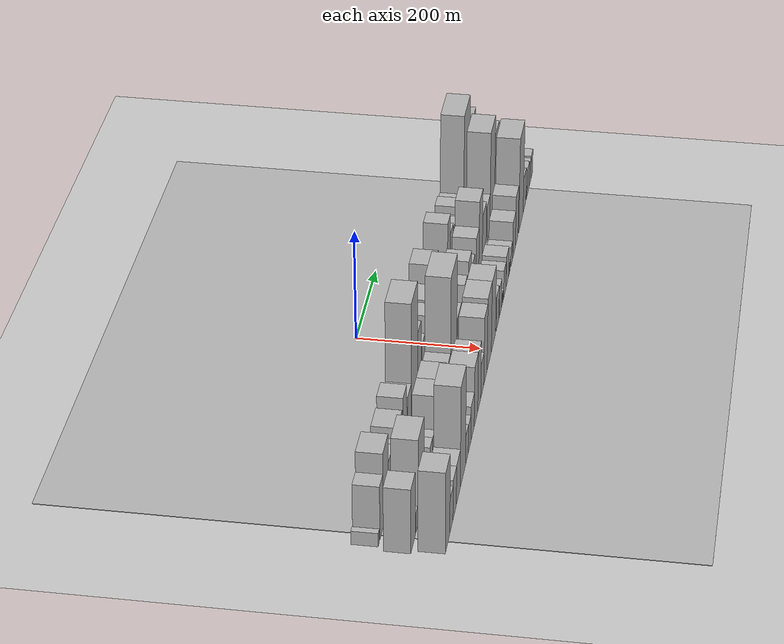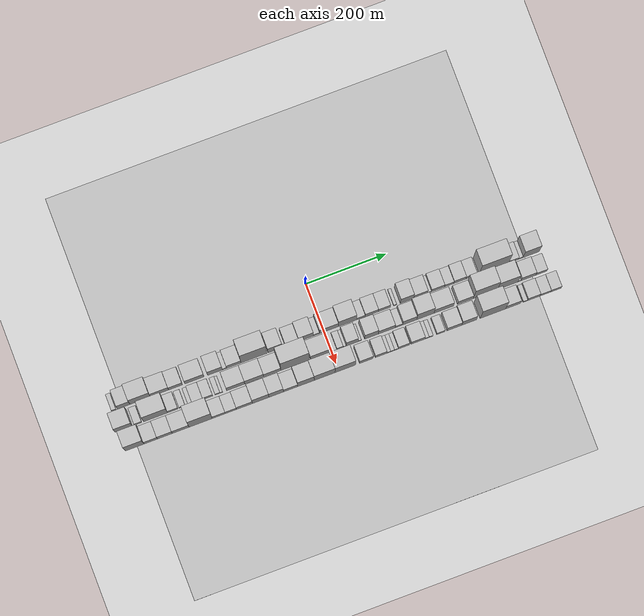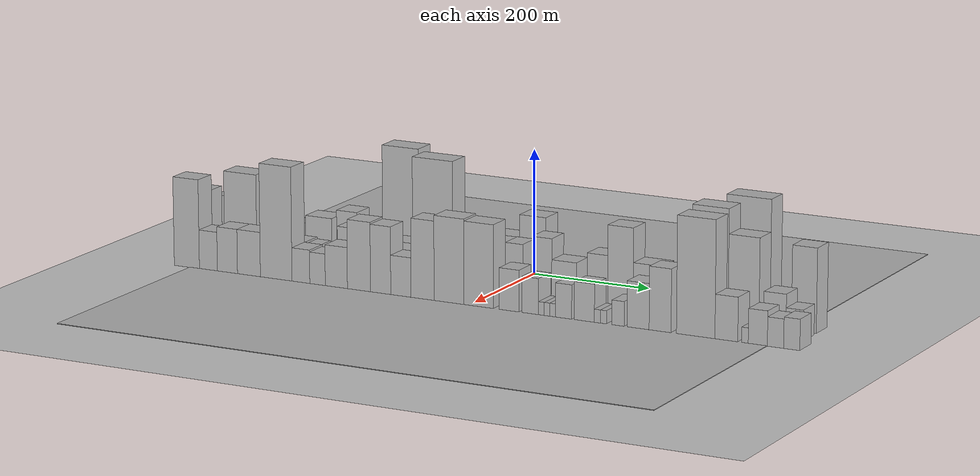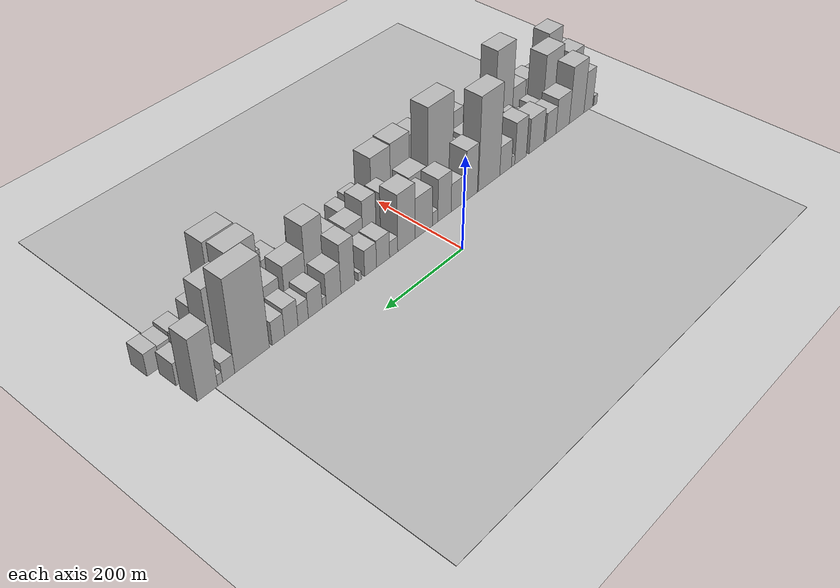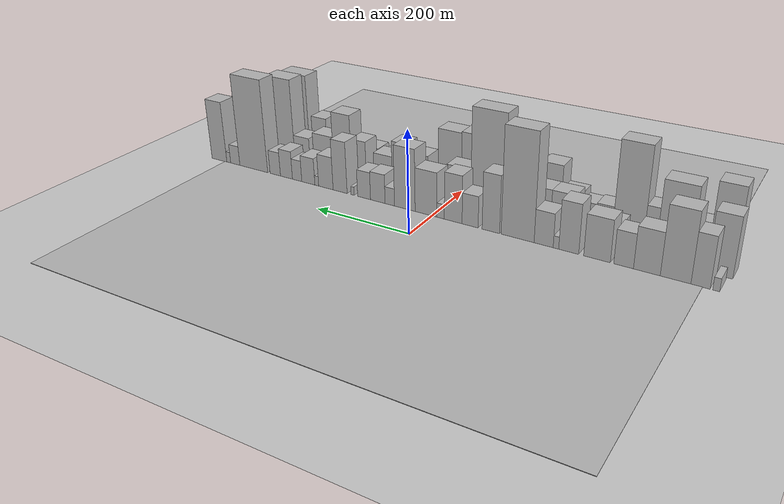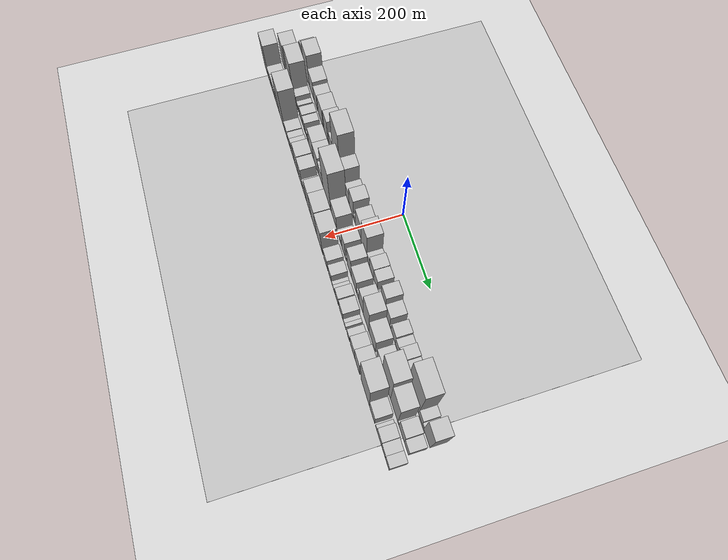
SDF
<?xml version="1.0" encoding="utf-8"?>

<sdf version="1.6">

   <world name="default">

      <gui fullscreen="0">

         <camera name="user_camera">

            <pose>-15 0 4.57585 0 0 0</pose>

            <view_controller>orbit</view_controller>

         </camera>

      </gui>

      <scene>

         <sky>

           <clouds>

             <speed>12</speed>

           </clouds>

         </sky>

         <ambient>0.4 0.4 0.4 1</ambient>

         <background>0.7 0.7 0.7 1</background>

         <shadows>1</shadows>

      </scene>

      <gravity>0 0 -9.8066</gravity>

      <magnetic_field>6e-06 2.3e-05 -4.2e-05</magnetic_field>

      <physics default="0" name="default_physics" type="ode">

         <ode>

            <solver>

               <type>quick</type>

               <iters>10</iters>

               <sor>1.0</sor>

               <use_dynamic_moi_rescaling>0</use_dynamic_moi_rescaling>

            </solver>

            <constraints>

               <cfm>0</cfm>

               <erp>0.2</erp>

               <contact_max_correcting_vel>100</contact_max_correcting_vel>

               <contact_surface_layer>0.001</contact_surface_layer>

            </constraints>

         </ode>

         <max_step_size>0.004</max_step_size>

         <real_time_factor>1</real_time_factor>

         <real_time_update_rate>250</real_time_update_rate>

      </physics>

      <light name="sun" type="directional">

         <cast_shadows>1</cast_shadows>

         <pose>0 0 10 0 0 0</pose>

         <diffuse>0.8 0.8 0.8 1</diffuse>

         <specular>0.2 0.2 0.2 1</specular>

         <attenuation>

            <range>1000</range>

            <constant>0.9</constant>

            <linear>0.01</linear>

            <quadratic>0.001</quadratic>

         </attenuation>

         <direction>-0.5 0.1 -0.9</direction>

      </light>

      <include>

         <name>ground_plane_1</name>

         <uri>model://HANNAS_ground_plane</uri>

         <pose>0 0 0  0 0 0</pose>

      </include>

      <include>

         <name>ground_plane_2</name>

         <uri>model://HANNAS_ground_plane</uri>

         <pose>100 0 0  0 0 0</pose>

      </include>

      <model name="building_1">

         <static>1</static>

         <pose frame="">100.0000 -521.4037 0 0.000000 0.000000 0.000000</pose>

         <link name="link">

            <pose frame="">0 0 12.00 0 0 0</pose>

            <collision name="collision">

               <geometry>

                  <box>

                     <size>40.0000 11.1926 24.0000</size>

                  </box>

               </geometry>

               <max_contacts>10</max_contacts>

               <surface>

                  <contact>

                     <ode/>

                  </contact>

                  <bounce/>

                  <friction>

                     <torsional>

                        <ode/>

                     </torsional>

                     <ode/>

                  </friction>

               </surface>

            </collision>

            <visual name="visual">

               <cast_shadows>0</cast_shadows>

               <geometry>

                  <box>

                     <size>40.0000 11.1926 24.0000</size>

                  </box>

               </geometry>

               <material>

                  <script>

                     <uri>model://HANNAS_wall/materials/scripts</uri>

                     <uri>model://HANNAS_wall/materials/textures</uri>

                     <name>vrc/HANNAS_wall</name>

                  </script>

               </material>

            </visual>

            <self_collide>0</self_collide>

            <enable_wind>0</enable_wind>

            <kinematic>0</kinematic>

         </link>

      </model>

      <model name="building_2">

         <static>1</static>

         <pose frame="">100.0000 -496.3942 0 0.000000 0.000000 0.000000</pose>

         <link name="link">

            <pose frame="">0 0 48.00 0 0 0</pose>

            <collision name="collision">

               <geometry>

                  <box>

                     <size>40.0000 30.8265 96.0000</size>

                  </box>

               </geometry>

               <max_contacts>10</max_contacts>

               <surface>

                  <contact>

                     <ode/>

                  </contact>

                  <bounce/>

                  <friction>

                     <torsional>

                        <ode/>

                     </torsional>

                     <ode/>

                  </friction>

               </surface>

            </collision>

            <visual name="visual">

               <cast_shadows>0</cast_shadows>

               <geometry>

                  <box>

                     <size>40.0000 30.8265 96.0000</size>

                  </box>

               </geometry>

               <material>

                  <script>

                     <uri>model://HANNAS_wall/materials/scripts</uri>

                     <uri>model://HANNAS_wall/materials/textures</uri>

                     <name>vrc/HANNAS_wall</name>

                  </script>

               </material>

            </visual>

            <self_collide>0</self_collide>

            <enable_wind>0</enable_wind>

            <kinematic>0</kinematic>

         </link>

      </model>

      <model name="building_3">

         <static>1</static>

         <pose frame="">100.0000 -455.8077 0 0.000000 0.000000 0.000000</pose>

         <link name="link">

            <pose frame="">0 0 66.00 0 0 0</pose>

            <collision name="collision">

               <geometry>

                  <box>

                     <size>40.0000 50.3465 132.0000</size>

                  </box>

               </geometry>

               <max_contacts>10</max_contacts>

               <surface>

                  <contact>

                     <ode/>

                  </contact>

                  <bounce/>

                  <friction>

                     <torsional>

                        <ode/>

                     </torsional>

                     <ode/>

                  </friction>

               </surface>

            </collision>

            <visual name="visual">

               <cast_shadows>0</cast_shadows>

               <geometry>

                  <box>

                     <size>40.0000 50.3465 132.0000</size>

                  </box>

               </geometry>

               <material>

                  <script>

                     <uri>model://HANNAS_wall/materials/scripts</uri>

                     <uri>model://HANNAS_wall/materials/textures</uri>

                     <name>vrc/HANNAS_wall</name>

                  </script>

               </material>

            </visual>

            <self_collide>0</self_collide>

            <enable_wind>0</enable_wind>

            <kinematic>0</kinematic>

         </link>

      </model>

      <model name="building_4">

         <static>1</static>

         <pose frame="">100.0000 -408.0286 0 0.000000 0.000000 0.000000</pose>

         <link name="link">

            <pose frame="">0 0 40.50 0 0 0</pose>

            <collision name="collision">

               <geometry>

                  <box>

                     <size>40.0000 45.2117 81.0000</size>

                  </box>

               </geometry>

               <max_contacts>10</max_contacts>

               <surface>

                  <contact>

                     <ode/>

                  </contact>

                  <bounce/>

                  <friction>

                     <torsional>

                        <ode/>

                     </torsional>

                     <ode/>

                  </friction>

               </surface>

            </collision>

            <visual name="visual">

               <cast_shadows>0</cast_shadows>

               <geometry>

                  <box>

                     <size>40.0000 45.2117 81.0000</size>

                  </box>

               </geometry>

               <material>

                  <script>

                     <uri>model://HANNAS_wall/materials/scripts</uri>

                     <uri>model://HANNAS_wall/materials/textures</uri>

                     <name>vrc/HANNAS_wall</name>

                  </script>

               </material>

            </visual>

            <self_collide>0</self_collide>

            <enable_wind>0</enable_wind>

            <kinematic>0</kinematic>

         </link>

      </model>

      <model name="building_5">

         <static>1</static>

         <pose frame="">100.0000 -368.3532 0 0.000000 0.000000 0.000000</pose>

         <link name="link">

            <pose frame="">0 0 33.00 0 0 0</pose>

            <collision name="collision">

               <geometry>

                  <box>

                     <size>40.0000 34.1391 66.0000</size>

                  </box>

               </geometry>

               <max_contacts>10</max_contacts>

               <surface>

                  <contact>

                     <ode/>

                  </contact>

                  <bounce/>

                  <friction>

                     <torsional>

                        <ode/>

                     </torsional>

                     <ode/>

                  </friction>

               </surface>

            </collision>

            <visual name="visual">

               <cast_shadows>0</cast_shadows>

               <geometry>

                  <box>

                     <size>40.0000 34.1391 66.0000</size>

                  </box>

               </geometry>

               <material>

                  <script>

                     <uri>model://HANNAS_wall/materials/scripts</uri>

                     <uri>model://HANNAS_wall/materials/textures</uri>

                     <name>vrc/HANNAS_wall</name>

                  </script>

               </material>

            </visual>

            <self_collide>0</self_collide>

            <enable_wind>0</enable_wind>

            <kinematic>0</kinematic>

         </link>

      </model>

      <model name="building_6">

         <static>1</static>

         <pose frame="">100.0000 -321.5796 0 0.000000 0.000000 0.000000</pose>

         <link name="link">

            <pose frame="">0 0 40.50 0 0 0</pose>

            <collision name="collision">

               <geometry>

                  <box>

                     <size>40.0000 47.4082 81.0000</size>

                  </box>

               </geometry>

               <max_contacts>10</max_contacts>

               <surface>

                  <contact>

                     <ode/>

                  </contact>

                  <bounce/>

                  <friction>

                     <torsional>

                        <ode/>

                     </torsional>

                     <ode/>

                  </friction>

               </surface>

            </collision>

            <visual name="visual">

               <cast_shadows>0</cast_shadows>

               <geometry>

                  <box>

                     <size>40.0000 47.4082 81.0000</size>

                  </box>

               </geometry>

               <material>

                  <script>

                     <uri>model://HANNAS_wall/materials/scripts</uri>

                     <uri>model://HANNAS_wall/materials/textures</uri>

                     <name>vrc/HANNAS_wall</name>

                  </script>

               </material>

            </visual>

            <self_collide>0</self_collide>

            <enable_wind>0</enable_wind>

            <kinematic>0</kinematic>

         </link>

      </model>

      <model name="building_7">

         <static>1</static>

         <pose frame="">100.0000 -270.5550 0 0.000000 0.000000 0.000000</pose>

         <link name="link">

            <pose frame="">0 0 48.00 0 0 0</pose>

            <collision name="collision">

               <geometry>

                  <box>

                     <size>40.0000 36.6409 96.0000</size>

                  </box>

               </geometry>

               <max_contacts>10</max_contacts>

               <surface>

                  <contact>

                     <ode/>

                  </contact>

                  <bounce/>

                  <friction>

                     <torsional>

                        <ode/>

                     </torsional>

                     <ode/>

                  </friction>

               </surface>

            </collision>

            <visual name="visual">

               <cast_shadows>0</cast_shadows>

               <geometry>

                  <box>

                     <size>40.0000 36.6409 96.0000</size>

                  </box>

               </geometry>

               <material>

                  <script>

                     <uri>model://HANNAS_wall/materials/scripts</uri>

                     <uri>model://HANNAS_wall/materials/textures</uri>

                     <name>vrc/HANNAS_wall</name>

                  </script>

               </material>

            </visual>

            <self_collide>0</self_collide>

            <enable_wind>0</enable_wind>

            <kinematic>0</kinematic>

         </link>

      </model>

      <model name="building_8">

         <static>1</static>

         <pose frame="">100.0000 -247.0979 0 0.000000 0.000000 0.000000</pose>

         <link name="link">

            <pose frame="">0 0 12.00 0 0 0</pose>

            <collision name="collision">

               <geometry>

                  <box>

                     <size>40.0000 10.2732 24.0000</size>

                  </box>

               </geometry>

               <max_contacts>10</max_contacts>

               <surface>

                  <contact>

                     <ode/>

                  </contact>

                  <bounce/>

                  <friction>

                     <torsional>

                        <ode/>

                     </torsional>

                     <ode/>

                  </friction>

               </surface>

            </collision>

            <visual name="visual">

               <cast_shadows>0</cast_shadows>

               <geometry>

                  <box>

                     <size>40.0000 10.2732 24.0000</size>

                  </box>

               </geometry>

               <material>

                  <script>

                     <uri>model://HANNAS_wall/materials/scripts</uri>

                     <uri>model://HANNAS_wall/materials/textures</uri>

                     <name>vrc/HANNAS_wall</name>

                  </script>

               </material>

            </visual>

            <self_collide>0</self_collide>

            <enable_wind>0</enable_wind>

            <kinematic>0</kinematic>

         </link>

      </model>

      <model name="building_9">

         <static>1</static>

         <pose frame="">100.0000 -224.0156 0 0.000000 0.000000 0.000000</pose>

         <link name="link">

            <pose frame="">0 0 33.00 0 0 0</pose>

            <collision name="collision">

               <geometry>

                  <box>

                     <size>40.0000 35.8916 66.0000</size>

                  </box>

               </geometry>

               <max_contacts>10</max_contacts>

               <surface>

                  <contact>

                     <ode/>

                  </contact>

                  <bounce/>

                  <friction>

                     <torsional>

                        <ode/>

                     </torsional>

                     <ode/>

                  </friction>

               </surface>

            </collision>

            <visual name="visual">

               <cast_shadows>0</cast_shadows>

               <geometry>

                  <box>

                     <size>40.0000 35.8916 66.0000</size>

                  </box>

               </geometry>

               <material>

                  <script>

                     <uri>model://HANNAS_wall/materials/scripts</uri>

                     <uri>model://HANNAS_wall/materials/textures</uri>

                     <name>vrc/HANNAS_wall</name>

                  </script>

               </material>

            </visual>

            <self_collide>0</self_collide>

            <enable_wind>0</enable_wind>

            <kinematic>0</kinematic>

         </link>

      </model>

      <model name="building_10">

         <static>1</static>

         <pose frame="">100.0000 -174.0560 0 0.000000 0.000000 0.000000</pose>

         <link name="link">

            <pose frame="">0 0 105.00 0 0 0</pose>

            <collision name="collision">

               <geometry>

                  <box>

                     <size>40.0000 64.0275 210.0000</size>

                  </box>

               </geometry>

               <max_contacts>10</max_contacts>

               <surface>

                  <contact>

                     <ode/>

                  </contact>

                  <bounce/>

                  <friction>

                     <torsional>

                        <ode/>

                     </torsional>

                     <ode/>

                  </friction>

               </surface>

            </collision>

            <visual name="visual">

               <cast_shadows>0</cast_shadows>

               <geometry>

                  <box>

                     <size>40.0000 64.0275 210.0000</size>

                  </box>

               </geometry>

               <material>

                  <script>

                     <uri>model://HANNAS_wall/materials/scripts</uri>

                     <uri>model://HANNAS_wall/materials/textures</uri>

                     <name>vrc/HANNAS_wall</name>

                  </script>

               </material>

            </visual>

            <self_collide>0</self_collide>

            <enable_wind>0</enable_wind>

            <kinematic>0</kinematic>

         </link>

      </model>

      <model name="building_11">

         <static>1</static>

         <pose frame="">100.0000 -121.6259 0 0.000000 0.000000 0.000000</pose>

         <link name="link">

            <pose frame="">0 0 57.00 0 0 0</pose>

            <collision name="collision">

               <geometry>

                  <box>

                     <size>40.0000 34.8327 114.0000</size>

                  </box>

               </geometry>

               <max_contacts>10</max_contacts>

               <surface>

                  <contact>

                     <ode/>

                  </contact>

                  <bounce/>

                  <friction>

                     <torsional>

                        <ode/>

                     </torsional>

                     <ode/>

                  </friction>

               </surface>

            </collision>

            <visual name="visual">

               <cast_shadows>0</cast_shadows>

               <geometry>

                  <box>

                     <size>40.0000 34.8327 114.0000</size>

                  </box>

               </geometry>

               <material>

                  <script>

                     <uri>model://HANNAS_wall/materials/scripts</uri>

                     <uri>model://HANNAS_wall/materials/textures</uri>

                     <name>vrc/HANNAS_wall</name>

                  </script>

               </material>

            </visual>

            <self_collide>0</self_collide>

            <enable_wind>0</enable_wind>

            <kinematic>0</kinematic>

         </link>

      </model>

      <model name="building_12">

         <static>1</static>

         <pose frame="">100.0000 -79.8092 0 0.000000 0.000000 0.000000</pose>

         <link name="link">

            <pose frame="">0 0 31.50 0 0 0</pose>

            <collision name="collision">

               <geometry>

                  <box>

                     <size>40.0000 32.8008 63.0000</size>

                  </box>

               </geometry>

               <max_contacts>10</max_contacts>

               <surface>

                  <contact>

                     <ode/>

                  </contact>

                  <bounce/>

                  <friction>

                     <torsional>

                        <ode/>

                     </torsional>

                     <ode/>

                  </friction>

               </surface>

            </collision>

            <visual name="visual">

               <cast_shadows>0</cast_shadows>

               <geometry>

                  <box>

                     <size>40.0000 32.8008 63.0000</size>

                  </box>

               </geometry>

               <material>

                  <script>

                     <uri>model://HANNAS_wall/materials/scripts</uri>

                     <uri>model://HANNAS_wall/materials/textures</uri>

                     <name>vrc/HANNAS_wall</name>

                  </script>

               </material>

            </visual>

            <self_collide>0</self_collide>

            <enable_wind>0</enable_wind>

            <kinematic>0</kinematic>

         </link>

      </model>

      <model name="building_13">

         <static>1</static>

         <pose frame="">100.0000 -44.9601 0 0.000000 0.000000 0.000000</pose>

         <link name="link">

            <pose frame="">0 0 48.00 0 0 0</pose>

            <collision name="collision">

               <geometry>

                  <box>

                     <size>40.0000 36.8974 96.0000</size>

                  </box>

               </geometry>

               <max_contacts>10</max_contacts>

               <surface>

                  <contact>

                     <ode/>

                  </contact>

                  <bounce/>

                  <friction>

                     <torsional>

                        <ode/>

                     </torsional>

                     <ode/>

                  </friction>

               </surface>

            </collision>

            <visual name="visual">

               <cast_shadows>0</cast_shadows>

               <geometry>

                  <box>

                     <size>40.0000 36.8974 96.0000</size>

                  </box>

               </geometry>

               <material>

                  <script>

                     <uri>model://HANNAS_wall/materials/scripts</uri>

                     <uri>model://HANNAS_wall/materials/textures</uri>

                     <name>vrc/HANNAS_wall</name>

                  </script>

               </material>

            </visual>

            <self_collide>0</self_collide>

            <enable_wind>0</enable_wind>

            <kinematic>0</kinematic>

         </link>

      </model>

      <model name="building_14">

         <static>1</static>

         <pose frame="">100.0000 -18.8374 0 0.000000 0.000000 0.000000</pose>

         <link name="link">

            <pose frame="">0 0 15.00 0 0 0</pose>

            <collision name="collision">

               <geometry>

                  <box>

                     <size>40.0000 15.3480 30.0000</size>

                  </box>

               </geometry>

               <max_contacts>10</max_contacts>

               <surface>

                  <contact>

                     <ode/>

                  </contact>

                  <bounce/>

                  <friction>

                     <torsional>

                        <ode/>

                     </torsional>

                     <ode/>

                  </friction>

               </surface>

            </collision>

            <visual name="visual">

               <cast_shadows>0</cast_shadows>

               <geometry>

                  <box>

                     <size>40.0000 15.3480 30.0000</size>

                  </box>

               </geometry>

               <material>

                  <script>

                     <uri>model://HANNAS_wall/materials/scripts</uri>

                     <uri>model://HANNAS_wall/materials/textures</uri>

                     <name>vrc/HANNAS_wall</name>

                  </script>

               </material>

            </visual>

            <self_collide>0</self_collide>

            <enable_wind>0</enable_wind>

            <kinematic>0</kinematic>

         </link>

      </model>

      <model name="building_15">

         <static>1</static>

         <pose frame="">100.0000 12.3434 0 0.000000 0.000000 0.000000</pose>

         <link name="link">

            <pose frame="">0 0 45.00 0 0 0</pose>

            <collision name="collision">

               <geometry>

                  <box>

                     <size>40.0000 47.0137 90.0000</size>

                  </box>

               </geometry>

               <max_contacts>10</max_contacts>

               <surface>

                  <contact>

                     <ode/>

                  </contact>

                  <bounce/>

                  <friction>

                     <torsional>

                        <ode/>

                     </torsional>

                     <ode/>

                  </friction>

               </surface>

            </collision>

            <visual name="visual">

               <cast_shadows>0</cast_shadows>

               <geometry>

                  <box>

                     <size>40.0000 47.0137 90.0000</size>

                  </box>

               </geometry>

               <material>

                  <script>

                     <uri>model://HANNAS_wall/materials/scripts</uri>

                     <uri>model://HANNAS_wall/materials/textures</uri>

                     <name>vrc/HANNAS_wall</name>

                  </script>

               </material>

            </visual>

            <self_collide>0</self_collide>

            <enable_wind>0</enable_wind>

            <kinematic>0</kinematic>

         </link>

      </model>

      <model name="building_16">

         <static>1</static>

         <pose frame="">100.0000 58.5204 0 0.000000 0.000000 0.000000</pose>

         <link name="link">

            <pose frame="">0 0 63.00 0 0 0</pose>

            <collision name="collision">

               <geometry>

                  <box>

                     <size>40.0000 45.3403 126.0000</size>

                  </box>

               </geometry>

               <max_contacts>10</max_contacts>

               <surface>

                  <contact>

                     <ode/>

                  </contact>

                  <bounce/>

                  <friction>

                     <torsional>

                        <ode/>

                     </torsional>

                     <ode/>

                  </friction>

               </surface>

            </collision>

            <visual name="visual">

               <cast_shadows>0</cast_shadows>

               <geometry>

                  <box>

                     <size>40.0000 45.3403 126.0000</size>

                  </box>

               </geometry>

               <material>

                  <script>

                     <uri>model://HANNAS_wall/materials/scripts</uri>

                     <uri>model://HANNAS_wall/materials/textures</uri>

                     <name>vrc/HANNAS_wall</name>

                  </script>

               </material>

            </visual>

            <self_collide>0</self_collide>

            <enable_wind>0</enable_wind>

            <kinematic>0</kinematic>

         </link>

      </model>

      <model name="building_17">

         <static>1</static>

         <pose frame="">100.0000 91.7804 0 0.000000 0.000000 0.000000</pose>

         <link name="link">

            <pose frame="">0 0 18.00 0 0 0</pose>

            <collision name="collision">

               <geometry>

                  <box>

                     <size>40.0000 21.1796 36.0000</size>

                  </box>

               </geometry>

               <max_contacts>10</max_contacts>

               <surface>

                  <contact>

                     <ode/>

                  </contact>

                  <bounce/>

                  <friction>

                     <torsional>

                        <ode/>

                     </torsional>

                     <ode/>

                  </friction>

               </surface>

            </collision>

            <visual name="visual">

               <cast_shadows>0</cast_shadows>

               <geometry>

                  <box>

                     <size>40.0000 21.1796 36.0000</size>

                  </box>

               </geometry>

               <material>

                  <script>

                     <uri>model://HANNAS_wall/materials/scripts</uri>

                     <uri>model://HANNAS_wall/materials/textures</uri>

                     <name>vrc/HANNAS_wall</name>

                  </script>

               </material>

            </visual>

            <self_collide>0</self_collide>

            <enable_wind>0</enable_wind>

            <kinematic>0</kinematic>

         </link>

      </model>

      <model name="building_18">

         <static>1</static>

         <pose frame="">100.0000 118.8908 0 0.000000 0.000000 0.000000</pose>

         <link name="link">

            <pose frame="">0 0 30.00 0 0 0</pose>

            <collision name="collision">

               <geometry>

                  <box>

                     <size>40.0000 33.0412 60.0000</size>

                  </box>

               </geometry>

               <max_contacts>10</max_contacts>

               <surface>

                  <contact>

                     <ode/>

                  </contact>

                  <bounce/>

                  <friction>

                     <torsional>

                        <ode/>

                     </torsional>

                     <ode/>

                  </friction>

               </surface>

            </collision>

            <visual name="visual">

               <cast_shadows>0</cast_shadows>

               <geometry>

                  <box>

                     <size>40.0000 33.0412 60.0000</size>

                  </box>

               </geometry>

               <material>

                  <script>

                     <uri>model://HANNAS_wall/materials/scripts</uri>

                     <uri>model://HANNAS_wall/materials/textures</uri>

                     <name>vrc/HANNAS_wall</name>

                  </script>

               </material>

            </visual>

            <self_collide>0</self_collide>

            <enable_wind>0</enable_wind>

            <kinematic>0</kinematic>

         </link>

      </model>

      <model name="building_19">

         <static>1</static>

         <pose frame="">100.0000 150.2969 0 0.000000 0.000000 0.000000</pose>

         <link name="link">

            <pose frame="">0 0 28.50 0 0 0</pose>

            <collision name="collision">

               <geometry>

                  <box>

                     <size>40.0000 29.7710 57.0000</size>

                  </box>

               </geometry>

               <max_contacts>10</max_contacts>

               <surface>

                  <contact>

                     <ode/>

                  </contact>

                  <bounce/>

                  <friction>

                     <torsional>

                        <ode/>

                     </torsional>

                     <ode/>

                  </friction>

               </surface>

            </collision>

            <visual name="visual">

               <cast_shadows>0</cast_shadows>

               <geometry>

                  <box>

                     <size>40.0000 29.7710 57.0000</size>

                  </box>

               </geometry>

               <material>

                  <script>

                     <uri>model://HANNAS_wall/materials/scripts</uri>

                     <uri>model://HANNAS_wall/materials/textures</uri>

                     <name>vrc/HANNAS_wall</name>

                  </script>

               </material>

            </visual>

            <self_collide>0</self_collide>

            <enable_wind>0</enable_wind>

            <kinematic>0</kinematic>

         </link>

      </model>

      <model name="building_20">

         <static>1</static>

         <pose frame="">100.0000 176.9472 0 0.000000 0.000000 0.000000</pose>

         <link name="link">

            <pose frame="">0 0 9.00 0 0 0</pose>

            <collision name="collision">

               <geometry>

                  <box>

                     <size>40.0000 7.5295 18.0000</size>

                  </box>

               </geometry>

               <max_contacts>10</max_contacts>

               <surface>

                  <contact>

                     <ode/>

                  </contact>

                  <bounce/>

                  <friction>

                     <torsional>

                        <ode/>

                     </torsional>

                     <ode/>

                  </friction>

               </surface>

            </collision>

            <visual name="visual">

               <cast_shadows>0</cast_shadows>

               <geometry>

                  <box>

                     <size>40.0000 7.5295 18.0000</size>

                  </box>

               </geometry>

               <material>

                  <script>

                     <uri>model://HANNAS_wall/materials/scripts</uri>

                     <uri>model://HANNAS_wall/materials/textures</uri>

                     <name>vrc/HANNAS_wall</name>

                  </script>

               </material>

            </visual>

            <self_collide>0</self_collide>

            <enable_wind>0</enable_wind>

            <kinematic>0</kinematic>

         </link>

      </model>

      <model name="building_21">

         <static>1</static>

         <pose frame="">100.0000 206.3508 0 0.000000 0.000000 0.000000</pose>

         <link name="link">

            <pose frame="">0 0 54.00 0 0 0</pose>

            <collision name="collision">

               <geometry>

                  <box>

                     <size>40.0000 33.2777 108.0000</size>

                  </box>

               </geometry>

               <max_contacts>10</max_contacts>

               <surface>

                  <contact>

                     <ode/>

                  </contact>

                  <bounce/>

                  <friction>

                     <torsional>

                        <ode/>

                     </torsional>

                     <ode/>

                  </friction>

               </surface>

            </collision>

            <visual name="visual">

               <cast_shadows>0</cast_shadows>

               <geometry>

                  <box>

                     <size>40.0000 33.2777 108.0000</size>

                  </box>

               </geometry>

               <material>

                  <script>

                     <uri>model://HANNAS_wall/materials/scripts</uri>

                     <uri>model://HANNAS_wall/materials/textures</uri>

                     <name>vrc/HANNAS_wall</name>

                  </script>

               </material>

            </visual>

            <self_collide>0</self_collide>

            <enable_wind>0</enable_wind>

            <kinematic>0</kinematic>

         </link>

      </model>

      <model name="building_22">

         <static>1</static>

         <pose frame="">100.0000 240.4741 0 0.000000 0.000000 0.000000</pose>

         <link name="link">

            <pose frame="">0 0 34.50 0 0 0</pose>

            <collision name="collision">

               <geometry>

                  <box>

                     <size>40.0000 34.9690 69.0000</size>

                  </box>

               </geometry>

               <max_contacts>10</max_contacts>

               <surface>

                  <contact>

                     <ode/>

                  </contact>

                  <bounce/>

                  <friction>

                     <torsional>

                        <ode/>

                     </torsional>

                     <ode/>

                  </friction>

               </surface>

            </collision>

            <visual name="visual">

               <cast_shadows>0</cast_shadows>

               <geometry>

                  <box>

                     <size>40.0000 34.9690 69.0000</size>

                  </box>

               </geometry>

               <material>

                  <script>

                     <uri>model://HANNAS_wall/materials/scripts</uri>

                     <uri>model://HANNAS_wall/materials/textures</uri>

                     <name>vrc/HANNAS_wall</name>

                  </script>

               </material>

            </visual>

            <self_collide>0</self_collide>

            <enable_wind>0</enable_wind>

            <kinematic>0</kinematic>

         </link>

      </model>

      <model name="building_23">

         <static>1</static>

         <pose frame="">100.0000 262.5453 0 0.000000 0.000000 0.000000</pose>

         <link name="link">

            <pose frame="">0 0 10.50 0 0 0</pose>

            <collision name="collision">

               <geometry>

                  <box>

                     <size>40.0000 9.1734 21.0000</size>

                  </box>

               </geometry>

               <max_contacts>10</max_contacts>

               <surface>

                  <contact>

                     <ode/>

                  </contact>

                  <bounce/>

                  <friction>

                     <torsional>

                        <ode/>

                     </torsional>

                     <ode/>

                  </friction>

               </surface>

            </collision>

            <visual name="visual">

               <cast_shadows>0</cast_shadows>

               <geometry>

                  <box>

                     <size>40.0000 9.1734 21.0000</size>

                  </box>

               </geometry>

               <material>

                  <script>

                     <uri>model://HANNAS_wall/materials/scripts</uri>

                     <uri>model://HANNAS_wall/materials/textures</uri>

                     <name>vrc/HANNAS_wall</name>

                  </script>

               </material>

            </visual>

            <self_collide>0</self_collide>

            <enable_wind>0</enable_wind>

            <kinematic>0</kinematic>

         </link>

      </model>

      <model name="building_24">

         <static>1</static>

         <pose frame="">100.0000 283.3164 0 0.000000 0.000000 0.000000</pose>

         <link name="link">

            <pose frame="">0 0 28.50 0 0 0</pose>

            <collision name="collision">

               <geometry>

                  <box>

                     <size>40.0000 32.3688 57.0000</size>

                  </box>

               </geometry>

               <max_contacts>10</max_contacts>

               <surface>

                  <contact>

                     <ode/>

                  </contact>

                  <bounce/>

                  <friction>

                     <torsional>

                        <ode/>

                     </torsional>

                     <ode/>

                  </friction>

               </surface>

            </collision>

            <visual name="visual">

               <cast_shadows>0</cast_shadows>

               <geometry>

                  <box>

                     <size>40.0000 32.3688 57.0000</size>

                  </box>

               </geometry>

               <material>

                  <script>

                     <uri>model://HANNAS_wall/materials/scripts</uri>

                     <uri>model://HANNAS_wall/materials/textures</uri>

                     <name>vrc/HANNAS_wall</name>

                  </script>

               </material>

            </visual>

            <self_collide>0</self_collide>

            <enable_wind>0</enable_wind>

            <kinematic>0</kinematic>

         </link>

      </model>

      <model name="building_25">

         <static>1</static>

         <pose frame="">100.0000 311.2265 0 0.000000 0.000000 0.000000</pose>

         <link name="link">

            <pose frame="">0 0 22.50 0 0 0</pose>

            <collision name="collision">

               <geometry>

                  <box>

                     <size>40.0000 23.4514 45.0000</size>

                  </box>

               </geometry>

               <max_contacts>10</max_contacts>

               <surface>

                  <contact>

                     <ode/>

                  </contact>

                  <bounce/>

                  <friction>

                     <torsional>

                        <ode/>

                     </torsional>

                     <ode/>

                  </friction>

               </surface>

            </collision>

            <visual name="visual">

               <cast_shadows>0</cast_shadows>

               <geometry>

                  <box>

                     <size>40.0000 23.4514 45.0000</size>

                  </box>

               </geometry>

               <material>

                  <script>

                     <uri>model://HANNAS_wall/materials/scripts</uri>

                     <uri>model://HANNAS_wall/materials/textures</uri>

                     <name>vrc/HANNAS_wall</name>

                  </script>

               </material>

            </visual>

            <self_collide>0</self_collide>

            <enable_wind>0</enable_wind>

            <kinematic>0</kinematic>

         </link>

      </model>

      <model name="building_26">

         <static>1</static>

         <pose frame="">100.0000 338.1147 0 0.000000 0.000000 0.000000</pose>

         <link name="link">

            <pose frame="">0 0 30.00 0 0 0</pose>

            <collision name="collision">

               <geometry>

                  <box>

                     <size>40.0000 30.3249 60.0000</size>

                  </box>

               </geometry>

               <max_contacts>10</max_contacts>

               <surface>

                  <contact>

                     <ode/>

                  </contact>

                  <bounce/>

                  <friction>

                     <torsional>

                        <ode/>

                     </torsional>

                     <ode/>

                  </friction>

               </surface>

            </collision>

            <visual name="visual">

               <cast_shadows>0</cast_shadows>

               <geometry>

                  <box>

                     <size>40.0000 30.3249 60.0000</size>

                  </box>

               </geometry>

               <material>

                  <script>

                     <uri>model://HANNAS_wall/materials/scripts</uri>

                     <uri>model://HANNAS_wall/materials/textures</uri>

                     <name>vrc/HANNAS_wall</name>

                  </script>

               </material>

            </visual>

            <self_collide>0</self_collide>

            <enable_wind>0</enable_wind>

            <kinematic>0</kinematic>

         </link>

      </model>

      <model name="building_27">

         <static>1</static>

         <pose frame="">100.0000 366.7676 0 0.000000 0.000000 0.000000</pose>

         <link name="link">

            <pose frame="">0 0 25.50 0 0 0</pose>

            <collision name="collision">

               <geometry>

                  <box>

                     <size>40.0000 26.9808 51.0000</size>

                  </box>

               </geometry>

               <max_contacts>10</max_contacts>

               <surface>

                  <contact>

                     <ode/>

                  </contact>

                  <bounce/>

                  <friction>

                     <torsional>

                        <ode/>

                     </torsional>

                     <ode/>

                  </friction>

               </surface>

            </collision>

            <visual name="visual">

               <cast_shadows>0</cast_shadows>

               <geometry>

                  <box>

                     <size>40.0000 26.9808 51.0000</size>

                  </box>

               </geometry>

               <material>

                  <script>

                     <uri>model://HANNAS_wall/materials/scripts</uri>

                     <uri>model://HANNAS_wall/materials/textures</uri>

                     <name>vrc/HANNAS_wall</name>

                  </script>

               </material>

            </visual>

            <self_collide>0</self_collide>

            <enable_wind>0</enable_wind>

            <kinematic>0</kinematic>

         </link>

      </model>

      <model name="building_28">

         <static>1</static>

         <pose frame="">100.0000 423.1120 0 0.000000 0.000000 0.000000</pose>

         <link name="link">

            <pose frame="">0 0 99.00 0 0 0</pose>

            <collision name="collision">

               <geometry>

                  <box>

                     <size>40.0000 73.7081 198.0000</size>

                  </box>

               </geometry>

               <max_contacts>10</max_contacts>

               <surface>

                  <contact>

                     <ode/>

                  </contact>

                  <bounce/>

                  <friction>

                     <torsional>

                        <ode/>

                     </torsional>

                     <ode/>

                  </friction>

               </surface>

            </collision>

            <visual name="visual">

               <cast_shadows>0</cast_shadows>

               <geometry>

                  <box>

                     <size>40.0000 73.7081 198.0000</size>

                  </box>

               </geometry>

               <material>

                  <script>

                     <uri>model://HANNAS_wall/materials/scripts</uri>

                     <uri>model://HANNAS_wall/materials/textures</uri>

                     <name>vrc/HANNAS_wall</name>

                  </script>

               </material>

            </visual>

            <self_collide>0</self_collide>

            <enable_wind>0</enable_wind>

            <kinematic>0</kinematic>

         </link>

      </model>

      <model name="building_29">

         <static>1</static>

         <pose frame="">100.0000 472.4163 0 0.000000 0.000000 0.000000</pose>

         <link name="link">

            <pose frame="">0 0 21.00 0 0 0</pose>

            <collision name="collision">

               <geometry>

                  <box>

                     <size>40.0000 24.9005 42.0000</size>

                  </box>

               </geometry>

               <max_contacts>10</max_contacts>

               <surface>

                  <contact>

                     <ode/>

                  </contact>

                  <bounce/>

                  <friction>

                     <torsional>

                        <ode/>

                     </torsional>

                     <ode/>

                  </friction>

               </surface>

            </collision>

            <visual name="visual">

               <cast_shadows>0</cast_shadows>

               <geometry>

                  <box>

                     <size>40.0000 24.9005 42.0000</size>

                  </box>

               </geometry>

               <material>

                  <script>

                     <uri>model://HANNAS_wall/materials/scripts</uri>

                     <uri>model://HANNAS_wall/materials/textures</uri>

                     <name>vrc/HANNAS_wall</name>

                  </script>

               </material>

            </visual>

            <self_collide>0</self_collide>

            <enable_wind>0</enable_wind>

            <kinematic>0</kinematic>

         </link>

      </model>

      <model name="building_30">

         <static>1</static>

         <pose frame="">100.0000 490.0651 0 0.000000 0.000000 0.000000</pose>

         <link name="link">

            <pose frame="">0 0 12.00 0 0 0</pose>

            <collision name="collision">

               <geometry>

                  <box>

                     <size>40.0000 10.3970 24.0000</size>

                  </box>

               </geometry>

               <max_contacts>10</max_contacts>

               <surface>

                  <contact>

                     <ode/>

                  </contact>

                  <bounce/>

                  <friction>

                     <torsional>

                        <ode/>

                     </torsional>

                     <ode/>

                  </friction>

               </surface>

            </collision>

            <visual name="visual">

               <cast_shadows>0</cast_shadows>

               <geometry>

                  <box>

                     <size>40.0000 10.3970 24.0000</size>

                  </box>

               </geometry>

               <material>

                  <script>

                     <uri>model://HANNAS_wall/materials/scripts</uri>

                     <uri>model://HANNAS_wall/materials/textures</uri>

                     <name>vrc/HANNAS_wall</name>

                  </script>

               </material>

            </visual>

            <self_collide>0</self_collide>

            <enable_wind>0</enable_wind>

            <kinematic>0</kinematic>

         </link>

      </model>

      <model name="building_31">

         <static>1</static>

         <pose frame="">100.0000 515.6405 0 0.000000 0.000000 0.000000</pose>

         <link name="link">

            <pose frame="">0 0 66.00 0 0 0</pose>

            <collision name="collision">

               <geometry>

                  <box>

                     <size>40.0000 40.7539 132.0000</size>

                  </box>

               </geometry>

               <max_contacts>10</max_contacts>

               <surface>

                  <contact>

                     <ode/>

                  </contact>

                  <bounce/>

                  <friction>

                     <torsional>

                        <ode/>

                     </torsional>

                     <ode/>

                  </friction>

               </surface>

            </collision>

            <visual name="visual">

               <cast_shadows>0</cast_shadows>

               <geometry>

                  <box>

                     <size>40.0000 40.7539 132.0000</size>

                  </box>

               </geometry>

               <material>

                  <script>

                     <uri>model://HANNAS_wall/materials/scripts</uri>

                     <uri>model://HANNAS_wall/materials/textures</uri>

                     <name>vrc/HANNAS_wall</name>

                  </script>

               </material>

            </visual>

            <self_collide>0</self_collide>

            <enable_wind>0</enable_wind>

            <kinematic>0</kinematic>

         </link>

      </model>

      <model name="building_32">

         <static>1</static>

         <pose frame="">149.0000 -514.9103 0 0.000000 0.000000 0.000000</pose>

         <link name="link">

            <pose frame="">0 0 57.00 0 0 0</pose>

            <collision name="collision">

               <geometry>

                  <box>

                     <size>40.0000 42.1795 114.0000</size>

                  </box>

               </geometry>

               <max_contacts>10</max_contacts>

               <surface>

                  <contact>

                     <ode/>

                  </contact>

                  <bounce/>

                  <friction>

                     <torsional>

                        <ode/>

                     </torsional>

                     <ode/>

                  </friction>

               </surface>

            </collision>

            <visual name="visual">

               <cast_shadows>0</cast_shadows>

               <geometry>

                  <box>

                     <size>40.0000 42.1795 114.0000</size>

                  </box>

               </geometry>

               <material>

                  <script>

                     <uri>model://HANNAS_wall/materials/scripts</uri>

                     <uri>model://HANNAS_wall/materials/textures</uri>

                     <name>vrc/HANNAS_wall</name>

                  </script>

               </material>

            </visual>

            <self_collide>0</self_collide>

            <enable_wind>0</enable_wind>

            <kinematic>0</kinematic>

         </link>

      </model>

      <model name="building_33">

         <static>1</static>

         <pose frame="">149.0000 -479.6092 0 0.000000 0.000000 0.000000</pose>

         <link name="link">

            <pose frame="">0 0 18.00 0 0 0</pose>

            <collision name="collision">

               <geometry>

                  <box>

                     <size>40.0000 18.4227 36.0000</size>

                  </box>

               </geometry>

               <max_contacts>10</max_contacts>

               <surface>

                  <contact>

                     <ode/>

                  </contact>

                  <bounce/>

                  <friction>

                     <torsional>

                        <ode/>

                     </torsional>

                     <ode/>

                  </friction>

               </surface>

            </collision>

            <visual name="visual">

               <cast_shadows>0</cast_shadows>

               <geometry>

                  <box>

                     <size>40.0000 18.4227 36.0000</size>

                  </box>

               </geometry>

               <material>

                  <script>

                     <uri>model://HANNAS_wall/materials/scripts</uri>

                     <uri>model://HANNAS_wall/materials/textures</uri>

                     <name>vrc/HANNAS_wall</name>

                  </script>

               </material>

            </visual>

            <self_collide>0</self_collide>

            <enable_wind>0</enable_wind>

            <kinematic>0</kinematic>

         </link>

      </model>

      <model name="building_34">

         <static>1</static>

         <pose frame="">149.0000 -435.8248 0 0.000000 0.000000 0.000000</pose>

         <link name="link">

            <pose frame="">0 0 75.00 0 0 0</pose>

            <collision name="collision">

               <geometry>

                  <box>

                     <size>40.0000 59.1461 150.0000</size>

                  </box>

               </geometry>

               <max_contacts>10</max_contacts>

               <surface>

                  <contact>

                     <ode/>

                  </contact>

                  <bounce/>

                  <friction>

                     <torsional>

                        <ode/>

                     </torsional>

                     <ode/>

                  </friction>

               </surface>

            </collision>

            <visual name="visual">

               <cast_shadows>0</cast_shadows>

               <geometry>

                  <box>

                     <size>40.0000 59.1461 150.0000</size>

                  </box>

               </geometry>

               <material>

                  <script>

                     <uri>model://HANNAS_wall/materials/scripts</uri>

                     <uri>model://HANNAS_wall/materials/textures</uri>

                     <name>vrc/HANNAS_wall</name>

                  </script>

               </material>

            </visual>

            <self_collide>0</self_collide>

            <enable_wind>0</enable_wind>

            <kinematic>0</kinematic>

         </link>

      </model>

      <model name="building_35">

         <static>1</static>

         <pose frame="">149.0000 -393.4889 0 0.000000 0.000000 0.000000</pose>

         <link name="link">

            <pose frame="">0 0 22.50 0 0 0</pose>

            <collision name="collision">

               <geometry>

                  <box>

                     <size>40.0000 25.5256 45.0000</size>

                  </box>

               </geometry>

               <max_contacts>10</max_contacts>

               <surface>

                  <contact>

                     <ode/>

                  </contact>

                  <bounce/>

                  <friction>

                     <torsional>

                        <ode/>

                     </torsional>

                     <ode/>

                  </friction>

               </surface>

            </collision>

            <visual name="visual">

               <cast_shadows>0</cast_shadows>

               <geometry>

                  <box>

                     <size>40.0000 25.5256 45.0000</size>

                  </box>

               </geometry>

               <material>

                  <script>

                     <uri>model://HANNAS_wall/materials/scripts</uri>

                     <uri>model://HANNAS_wall/materials/textures</uri>

                     <name>vrc/HANNAS_wall</name>

                  </script>

               </material>

            </visual>

            <self_collide>0</self_collide>

            <enable_wind>0</enable_wind>

            <kinematic>0</kinematic>

         </link>

      </model>

      <model name="building_36">

         <static>1</static>

         <pose frame="">149.0000 -370.1342 0 0.000000 0.000000 0.000000</pose>

         <link name="link">

            <pose frame="">0 0 15.00 0 0 0</pose>

            <collision name="collision">

               <geometry>

                  <box>

                     <size>40.0000 15.1838 30.0000</size>

                  </box>

               </geometry>

               <max_contacts>10</max_contacts>

               <surface>

                  <contact>

                     <ode/>

                  </contact>

                  <bounce/>

                  <friction>

                     <torsional>

                        <ode/>

                     </torsional>

                     <ode/>

                  </friction>

               </surface>

            </collision>

            <visual name="visual">

               <cast_shadows>0</cast_shadows>

               <geometry>

                  <box>

                     <size>40.0000 15.1838 30.0000</size>

                  </box>

               </geometry>

               <material>

                  <script>

                     <uri>model://HANNAS_wall/materials/scripts</uri>

                     <uri>model://HANNAS_wall/materials/textures</uri>

                     <name>vrc/HANNAS_wall</name>

                  </script>

               </material>

            </visual>

            <self_collide>0</self_collide>

            <enable_wind>0</enable_wind>

            <kinematic>0</kinematic>

         </link>

      </model>

      <model name="building_37">

         <static>1</static>

         <pose frame="">149.0000 -350.5875 0 0.000000 0.000000 0.000000</pose>

         <link name="link">

            <pose frame="">0 0 12.00 0 0 0</pose>

            <collision name="collision">

               <geometry>

                  <box>

                     <size>40.0000 9.9095 24.0000</size>

                  </box>

               </geometry>

               <max_contacts>10</max_contacts>

               <surface>

                  <contact>

                     <ode/>

                  </contact>

                  <bounce/>

                  <friction>

                     <torsional>

                        <ode/>

                     </torsional>

                     <ode/>

                  </friction>

               </surface>

            </collision>

            <visual name="visual">

               <cast_shadows>0</cast_shadows>

               <geometry>

                  <box>

                     <size>40.0000 9.9095 24.0000</size>

                  </box>

               </geometry>

               <material>

                  <script>

                     <uri>model://HANNAS_wall/materials/scripts</uri>

                     <uri>model://HANNAS_wall/materials/textures</uri>

                     <name>vrc/HANNAS_wall</name>

                  </script>

               </material>

            </visual>

            <self_collide>0</self_collide>

            <enable_wind>0</enable_wind>

            <kinematic>0</kinematic>

         </link>

      </model>

      <model name="building_38">

         <static>1</static>

         <pose frame="">149.0000 -332.2537 0 0.000000 0.000000 0.000000</pose>

         <link name="link">

            <pose frame="">0 0 25.50 0 0 0</pose>

            <collision name="collision">

               <geometry>

                  <box>

                     <size>40.0000 26.7582 51.0000</size>

                  </box>

               </geometry>

               <max_contacts>10</max_contacts>

               <surface>

                  <contact>

                     <ode/>

                  </contact>

                  <bounce/>

                  <friction>

                     <torsional>

                        <ode/>

                     </torsional>

                     <ode/>

                  </friction>

               </surface>

            </collision>

            <visual name="visual">

               <cast_shadows>0</cast_shadows>

               <geometry>

                  <box>

                     <size>40.0000 26.7582 51.0000</size>

                  </box>

               </geometry>

               <material>

                  <script>

                     <uri>model://HANNAS_wall/materials/scripts</uri>

                     <uri>model://HANNAS_wall/materials/textures</uri>

                     <name>vrc/HANNAS_wall</name>

                  </script>

               </material>

            </visual>

            <self_collide>0</self_collide>

            <enable_wind>0</enable_wind>

            <kinematic>0</kinematic>

         </link>

      </model>

      <model name="building_39">

         <static>1</static>

         <pose frame="">149.0000 -306.7413 0 0.000000 0.000000 0.000000</pose>

         <link name="link">

            <pose frame="">0 0 24.00 0 0 0</pose>

            <collision name="collision">

               <geometry>

                  <box>

                     <size>40.0000 24.2666 48.0000</size>

                  </box>

               </geometry>

               <max_contacts>10</max_contacts>

               <surface>

                  <contact>

                     <ode/>

                  </contact>

                  <bounce/>

                  <friction>

                     <torsional>

                        <ode/>

                     </torsional>

                     <ode/>

                  </friction>

               </surface>

            </collision>

            <visual name="visual">

               <cast_shadows>0</cast_shadows>

               <geometry>

                  <box>

                     <size>40.0000 24.2666 48.0000</size>

                  </box>

               </geometry>

               <material>

                  <script>

                     <uri>model://HANNAS_wall/materials/scripts</uri>

                     <uri>model://HANNAS_wall/materials/textures</uri>

                     <name>vrc/HANNAS_wall</name>

                  </script>

               </material>

            </visual>

            <self_collide>0</self_collide>

            <enable_wind>0</enable_wind>

            <kinematic>0</kinematic>

         </link>

      </model>

      <model name="building_40">

         <static>1</static>

         <pose frame="">149.0000 -282.5725 0 0.000000 0.000000 0.000000</pose>

         <link name="link">

            <pose frame="">0 0 13.50 0 0 0</pose>

            <collision name="collision">

               <geometry>

                  <box>

                     <size>40.0000 12.0711 27.0000</size>

                  </box>

               </geometry>

               <max_contacts>10</max_contacts>

               <surface>

                  <contact>

                     <ode/>

                  </contact>

                  <bounce/>

                  <friction>

                     <torsional>

                        <ode/>

                     </torsional>

                     <ode/>

                  </friction>

               </surface>

            </collision>

            <visual name="visual">

               <cast_shadows>0</cast_shadows>

               <geometry>

                  <box>

                     <size>40.0000 12.0711 27.0000</size>

                  </box>

               </geometry>

               <material>

                  <script>

                     <uri>model://HANNAS_wall/materials/scripts</uri>

                     <uri>model://HANNAS_wall/materials/textures</uri>

                     <name>vrc/HANNAS_wall</name>

                  </script>

               </material>

            </visual>

            <self_collide>0</self_collide>

            <enable_wind>0</enable_wind>

            <kinematic>0</kinematic>

         </link>

      </model>

      <model name="building_41">

         <static>1</static>

         <pose frame="">149.0000 -273.2129 0 0.000000 0.000000 0.000000</pose>

         <link name="link">

            <pose frame="">0 0 7.50 0 0 0</pose>

            <collision name="collision">

               <geometry>

                  <box>

                     <size>40.0000 6.6481 15.0000</size>

                  </box>

               </geometry>

               <max_contacts>10</max_contacts>

               <surface>

                  <contact>

                     <ode/>

                  </contact>

                  <bounce/>

                  <friction>

                     <torsional>

                        <ode/>

                     </torsional>

                     <ode/>

                  </friction>

               </surface>

            </collision>

            <visual name="visual">

               <cast_shadows>0</cast_shadows>

               <geometry>

                  <box>

                     <size>40.0000 6.6481 15.0000</size>

                  </box>

               </geometry>

               <material>

                  <script>

                     <uri>model://HANNAS_wall/materials/scripts</uri>

                     <uri>model://HANNAS_wall/materials/textures</uri>

                     <name>vrc/HANNAS_wall</name>

                  </script>

               </material>

            </visual>

            <self_collide>0</self_collide>

            <enable_wind>0</enable_wind>

            <kinematic>0</kinematic>

         </link>

      </model>

      <model name="building_42">

         <static>1</static>

         <pose frame="">149.0000 -237.4442 0 0.000000 0.000000 0.000000</pose>

         <link name="link">

            <pose frame="">0 0 42.00 0 0 0</pose>

            <collision name="collision">

               <geometry>

                  <box>

                     <size>40.0000 44.8894 84.0000</size>

                  </box>

               </geometry>

               <max_contacts>10</max_contacts>

               <surface>

                  <contact>

                     <ode/>

                  </contact>

                  <bounce/>

                  <friction>

                     <torsional>

                        <ode/>

                     </torsional>

                     <ode/>

                  </friction>

               </surface>

            </collision>

            <visual name="visual">

               <cast_shadows>0</cast_shadows>

               <geometry>

                  <box>

                     <size>40.0000 44.8894 84.0000</size>

                  </box>

               </geometry>

               <material>

                  <script>

                     <uri>model://HANNAS_wall/materials/scripts</uri>

                     <uri>model://HANNAS_wall/materials/textures</uri>

                     <name>vrc/HANNAS_wall</name>

                  </script>

               </material>

            </visual>

            <self_collide>0</self_collide>

            <enable_wind>0</enable_wind>

            <kinematic>0</kinematic>

         </link>

      </model>

      <model name="building_43">

         <static>1</static>

         <pose frame="">149.0000 -191.5692 0 0.000000 0.000000 0.000000</pose>

         <link name="link">

            <pose frame="">0 0 42.00 0 0 0</pose>

            <collision name="collision">

               <geometry>

                  <box>

                     <size>40.0000 46.8606 84.0000</size>

                  </box>

               </geometry>

               <max_contacts>10</max_contacts>

               <surface>

                  <contact>

                     <ode/>

                  </contact>

                  <bounce/>

                  <friction>

                     <torsional>

                        <ode/>

                     </torsional>

                     <ode/>

                  </friction>

               </surface>

            </collision>

            <visual name="visual">

               <cast_shadows>0</cast_shadows>

               <geometry>

                  <box>

                     <size>40.0000 46.8606 84.0000</size>

                  </box>

               </geometry>

               <material>

                  <script>

                     <uri>model://HANNAS_wall/materials/scripts</uri>

                     <uri>model://HANNAS_wall/materials/textures</uri>

                     <name>vrc/HANNAS_wall</name>

                  </script>

               </material>

            </visual>

            <self_collide>0</self_collide>

            <enable_wind>0</enable_wind>

            <kinematic>0</kinematic>

         </link>

      </model>

      <model name="building_44">

         <static>1</static>

         <pose frame="">149.0000 -146.8009 0 0.000000 0.000000 0.000000</pose>

         <link name="link">

            <pose frame="">0 0 36.00 0 0 0</pose>

            <collision name="collision">

               <geometry>

                  <box>

                     <size>40.0000 42.6759 72.0000</size>

                  </box>

               </geometry>

               <max_contacts>10</max_contacts>

               <surface>

                  <contact>

                     <ode/>

                  </contact>

                  <bounce/>

                  <friction>

                     <torsional>

                        <ode/>

                     </torsional>

                     <ode/>

                  </friction>

               </surface>

            </collision>

            <visual name="visual">

               <cast_shadows>0</cast_shadows>

               <geometry>

                  <box>

                     <size>40.0000 42.6759 72.0000</size>

                  </box>

               </geometry>

               <material>

                  <script>

                     <uri>model://HANNAS_wall/materials/scripts</uri>

                     <uri>model://HANNAS_wall/materials/textures</uri>

                     <name>vrc/HANNAS_wall</name>

                  </script>

               </material>

            </visual>

            <self_collide>0</self_collide>

            <enable_wind>0</enable_wind>

            <kinematic>0</kinematic>

         </link>

      </model>

      <model name="building_45">

         <static>1</static>

         <pose frame="">149.0000 -90.2303 0 0.000000 0.000000 0.000000</pose>

         <link name="link">

            <pose frame="">0 0 105.00 0 0 0</pose>

            <collision name="collision">

               <geometry>

                  <box>

                     <size>40.0000 70.4652 210.0000</size>

                  </box>

               </geometry>

               <max_contacts>10</max_contacts>

               <surface>

                  <contact>

                     <ode/>

                  </contact>

                  <bounce/>

                  <friction>

                     <torsional>

                        <ode/>

                     </torsional>

                     <ode/>

                  </friction>

               </surface>

            </collision>

            <visual name="visual">

               <cast_shadows>0</cast_shadows>

               <geometry>

                  <box>

                     <size>40.0000 70.4652 210.0000</size>

                  </box>

               </geometry>

               <material>

                  <script>

                     <uri>model://HANNAS_wall/materials/scripts</uri>

                     <uri>model://HANNAS_wall/materials/textures</uri>

                     <name>vrc/HANNAS_wall</name>

                  </script>

               </material>

            </visual>

            <self_collide>0</self_collide>

            <enable_wind>0</enable_wind>

            <kinematic>0</kinematic>

         </link>

      </model>

      <model name="building_46">

         <static>1</static>

         <pose frame="">149.0000 -28.0417 0 0.000000 0.000000 0.000000</pose>

         <link name="link">

            <pose frame="">0 0 43.50 0 0 0</pose>

            <collision name="collision">

               <geometry>

                  <box>

                     <size>40.0000 47.9121 87.0000</size>

                  </box>

               </geometry>

               <max_contacts>10</max_contacts>

               <surface>

                  <contact>

                     <ode/>

                  </contact>

                  <bounce/>

                  <friction>

                     <torsional>

                        <ode/>

                     </torsional>

                     <ode/>

                  </friction>

               </surface>

            </collision>

            <visual name="visual">

               <cast_shadows>0</cast_shadows>

               <geometry>

                  <box>

                     <size>40.0000 47.9121 87.0000</size>

                  </box>

               </geometry>

               <material>

                  <script>

                     <uri>model://HANNAS_wall/materials/scripts</uri>

                     <uri>model://HANNAS_wall/materials/textures</uri>

                     <name>vrc/HANNAS_wall</name>

                  </script>

               </material>

            </visual>

            <self_collide>0</self_collide>

            <enable_wind>0</enable_wind>

            <kinematic>0</kinematic>

         </link>

      </model>

      <model name="building_47">

         <static>1</static>

         <pose frame="">149.0000 -0.2553 0 0.000000 0.000000 0.000000</pose>

         <link name="link">

            <pose frame="">0 0 9.00 0 0 0</pose>

            <collision name="collision">

               <geometry>

                  <box>

                     <size>40.0000 7.6607 18.0000</size>

                  </box>

               </geometry>

               <max_contacts>10</max_contacts>

               <surface>

                  <contact>

                     <ode/>

                  </contact>

                  <bounce/>

                  <friction>

                     <torsional>

                        <ode/>

                     </torsional>

                     <ode/>

                  </friction>

               </surface>

            </collision>

            <visual name="visual">

               <cast_shadows>0</cast_shadows>

               <geometry>

                  <box>

                     <size>40.0000 7.6607 18.0000</size>

                  </box>

               </geometry>

               <material>

                  <script>

                     <uri>model://HANNAS_wall/materials/scripts</uri>

                     <uri>model://HANNAS_wall/materials/textures</uri>

                     <name>vrc/HANNAS_wall</name>

                  </script>

               </material>

            </visual>

            <self_collide>0</self_collide>

            <enable_wind>0</enable_wind>

            <kinematic>0</kinematic>

         </link>

      </model>

      <model name="building_48">

         <static>1</static>

         <pose frame="">149.0000 21.4753 0 0.000000 0.000000 0.000000</pose>

         <link name="link">

            <pose frame="">0 0 15.00 0 0 0</pose>

            <collision name="collision">

               <geometry>

                  <box>

                     <size>40.0000 15.8003 30.0000</size>

                  </box>

               </geometry>

               <max_contacts>10</max_contacts>

               <surface>

                  <contact>

                     <ode/>

                  </contact>

                  <bounce/>

                  <friction>

                     <torsional>

                        <ode/>

                     </torsional>

                     <ode/>

                  </friction>

               </surface>

            </collision>

            <visual name="visual">

               <cast_shadows>0</cast_shadows>

               <geometry>

                  <box>

                     <size>40.0000 15.8003 30.0000</size>

                  </box>

               </geometry>

               <material>

                  <script>

                     <uri>model://HANNAS_wall/materials/scripts</uri>

                     <uri>model://HANNAS_wall/materials/textures</uri>

                     <name>vrc/HANNAS_wall</name>

                  </script>

               </material>

            </visual>

            <self_collide>0</self_collide>

            <enable_wind>0</enable_wind>

            <kinematic>0</kinematic>

         </link>

      </model>

      <model name="building_49">

         <static>1</static>

         <pose frame="">149.0000 33.0678 0 0.000000 0.000000 0.000000</pose>

         <link name="link">

            <pose frame="">0 0 7.50 0 0 0</pose>

            <collision name="collision">

               <geometry>

                  <box>

                     <size>40.0000 7.3847 15.0000</size>

                  </box>

               </geometry>

               <max_contacts>10</max_contacts>

               <surface>

                  <contact>

                     <ode/>

                  </contact>

                  <bounce/>

                  <friction>

                     <torsional>

                        <ode/>

                     </torsional>

                     <ode/>

                  </friction>

               </surface>

            </collision>

            <visual name="visual">

               <cast_shadows>0</cast_shadows>

               <geometry>

                  <box>

                     <size>40.0000 7.3847 15.0000</size>

                  </box>

               </geometry>

               <material>

                  <script>

                     <uri>model://HANNAS_wall/materials/scripts</uri>

                     <uri>model://HANNAS_wall/materials/textures</uri>

                     <name>vrc/HANNAS_wall</name>

                  </script>

               </material>

            </visual>

            <self_collide>0</self_collide>

            <enable_wind>0</enable_wind>

            <kinematic>0</kinematic>

         </link>

      </model>

      <model name="building_50">

         <static>1</static>

         <pose frame="">149.0000 51.7305 0 0.000000 0.000000 0.000000</pose>

         <link name="link">

            <pose frame="">0 0 46.50 0 0 0</pose>

            <collision name="collision">

               <geometry>

                  <box>

                     <size>40.0000 29.9406 93.0000</size>

                  </box>

               </geometry>

               <max_contacts>10</max_contacts>

               <surface>

                  <contact>

                     <ode/>

                  </contact>

                  <bounce/>

                  <friction>

                     <torsional>

                        <ode/>

                     </torsional>

                     <ode/>

                  </friction>

               </surface>

            </collision>

            <visual name="visual">

               <cast_shadows>0</cast_shadows>

               <geometry>

                  <box>

                     <size>40.0000 29.9406 93.0000</size>

                  </box>

               </geometry>

               <material>

                  <script>

                     <uri>model://HANNAS_wall/materials/scripts</uri>

                     <uri>model://HANNAS_wall/materials/textures</uri>

                     <name>vrc/HANNAS_wall</name>

                  </script>

               </material>

            </visual>

            <self_collide>0</self_collide>

            <enable_wind>0</enable_wind>

            <kinematic>0</kinematic>

         </link>

      </model>

      <model name="building_51">

         <static>1</static>

         <pose frame="">149.0000 70.6586 0 0.000000 0.000000 0.000000</pose>

         <link name="link">

            <pose frame="">0 0 9.00 0 0 0</pose>

            <collision name="collision">

               <geometry>

                  <box>

                     <size>40.0000 7.9157 18.0000</size>

                  </box>

               </geometry>

               <max_contacts>10</max_contacts>

               <surface>

                  <contact>

                     <ode/>

                  </contact>

                  <bounce/>

                  <friction>

                     <torsional>

                        <ode/>

                     </torsional>

                     <ode/>

                  </friction>

               </surface>

            </collision>

            <visual name="visual">

               <cast_shadows>0</cast_shadows>

               <geometry>

                  <box>

                     <size>40.0000 7.9157 18.0000</size>

                  </box>

               </geometry>

               <material>

                  <script>

                     <uri>model://HANNAS_wall/materials/scripts</uri>

                     <uri>model://HANNAS_wall/materials/textures</uri>

                     <name>vrc/HANNAS_wall</name>

                  </script>

               </material>

            </visual>

            <self_collide>0</self_collide>

            <enable_wind>0</enable_wind>

            <kinematic>0</kinematic>

         </link>

      </model>

      <model name="building_52">

         <static>1</static>

         <pose frame="">149.0000 99.5877 0 0.000000 0.000000 0.000000</pose>

         <link name="link">

            <pose frame="">0 0 54.00 0 0 0</pose>

            <collision name="collision">

               <geometry>

                  <box>

                     <size>40.0000 33.9426 108.0000</size>

                  </box>

               </geometry>

               <max_contacts>10</max_contacts>

               <surface>

                  <contact>

                     <ode/>

                  </contact>

                  <bounce/>

                  <friction>

                     <torsional>

                        <ode/>

                     </torsional>

                     <ode/>

                  </friction>

               </surface>

            </collision>

            <visual name="visual">

               <cast_shadows>0</cast_shadows>

               <geometry>

                  <box>

                     <size>40.0000 33.9426 108.0000</size>

                  </box>

               </geometry>

               <material>

                  <script>

                     <uri>model://HANNAS_wall/materials/scripts</uri>

                     <uri>model://HANNAS_wall/materials/textures</uri>

                     <name>vrc/HANNAS_wall</name>

                  </script>

               </material>

            </visual>

            <self_collide>0</self_collide>

            <enable_wind>0</enable_wind>

            <kinematic>0</kinematic>

         </link>

      </model>

      <model name="building_53">

         <static>1</static>

         <pose frame="">149.0000 137.5816 0 0.000000 0.000000 0.000000</pose>

         <link name="link">

            <pose frame="">0 0 37.50 0 0 0</pose>

            <collision name="collision">

               <geometry>

                  <box>

                     <size>40.0000 42.0452 75.0000</size>

                  </box>

               </geometry>

               <max_contacts>10</max_contacts>

               <surface>

                  <contact>

                     <ode/>

                  </contact>

                  <bounce/>

                  <friction>

                     <torsional>

                        <ode/>

                     </torsional>

                     <ode/>

                  </friction>

               </surface>

            </collision>

            <visual name="visual">

               <cast_shadows>0</cast_shadows>

               <geometry>

                  <box>

                     <size>40.0000 42.0452 75.0000</size>

                  </box>

               </geometry>

               <material>

                  <script>

                     <uri>model://HANNAS_wall/materials/scripts</uri>

                     <uri>model://HANNAS_wall/materials/textures</uri>

                     <name>vrc/HANNAS_wall</name>

                  </script>

               </material>

            </visual>

            <self_collide>0</self_collide>

            <enable_wind>0</enable_wind>

            <kinematic>0</kinematic>

         </link>

      </model>

      <model name="building_54">

         <static>1</static>

         <pose frame="">149.0000 167.7839 0 0.000000 0.000000 0.000000</pose>

         <link name="link">

            <pose frame="">0 0 18.00 0 0 0</pose>

            <collision name="collision">

               <geometry>

                  <box>

                     <size>40.0000 18.3594 36.0000</size>

                  </box>

               </geometry>

               <max_contacts>10</max_contacts>

               <surface>

                  <contact>

                     <ode/>

                  </contact>

                  <bounce/>

                  <friction>

                     <torsional>

                        <ode/>

                     </torsional>

                     <ode/>

                  </friction>

               </surface>

            </collision>

            <visual name="visual">

               <cast_shadows>0</cast_shadows>

               <geometry>

                  <box>

                     <size>40.0000 18.3594 36.0000</size>

                  </box>

               </geometry>

               <material>

                  <script>

                     <uri>model://HANNAS_wall/materials/scripts</uri>

                     <uri>model://HANNAS_wall/materials/textures</uri>

                     <name>vrc/HANNAS_wall</name>

                  </script>

               </material>

            </visual>

            <self_collide>0</self_collide>

            <enable_wind>0</enable_wind>

            <kinematic>0</kinematic>

         </link>

      </model>

      <model name="building_55">

         <static>1</static>

         <pose frame="">149.0000 194.4452 0 0.000000 0.000000 0.000000</pose>

         <link name="link">

            <pose frame="">0 0 46.50 0 0 0</pose>

            <collision name="collision">

               <geometry>

                  <box>

                     <size>40.0000 34.9633 93.0000</size>

                  </box>

               </geometry>

               <max_contacts>10</max_contacts>

               <surface>

                  <contact>

                     <ode/>

                  </contact>

                  <bounce/>

                  <friction>

                     <torsional>

                        <ode/>

                     </torsional>

                     <ode/>

                  </friction>

               </surface>

            </collision>

            <visual name="visual">

               <cast_shadows>0</cast_shadows>

               <geometry>

                  <box>

                     <size>40.0000 34.9633 93.0000</size>

                  </box>

               </geometry>

               <material>

                  <script>

                     <uri>model://HANNAS_wall/materials/scripts</uri>

                     <uri>model://HANNAS_wall/materials/textures</uri>

                     <name>vrc/HANNAS_wall</name>

                  </script>

               </material>

            </visual>

            <self_collide>0</self_collide>

            <enable_wind>0</enable_wind>

            <kinematic>0</kinematic>

         </link>

      </model>

      <model name="building_56">

         <static>1</static>

         <pose frame="">149.0000 233.4893 0 0.000000 0.000000 0.000000</pose>

         <link name="link">

            <pose frame="">0 0 70.50 0 0 0</pose>

            <collision name="collision">

               <geometry>

                  <box>

                     <size>40.0000 43.1250 141.0000</size>

                  </box>

               </geometry>

               <max_contacts>10</max_contacts>

               <surface>

                  <contact>

                     <ode/>

                  </contact>

                  <bounce/>

                  <friction>

                     <torsional>

                        <ode/>

                     </torsional>

                     <ode/>

                  </friction>

               </surface>

            </collision>

            <visual name="visual">

               <cast_shadows>0</cast_shadows>

               <geometry>

                  <box>

                     <size>40.0000 43.1250 141.0000</size>

                  </box>

               </geometry>

               <material>

                  <script>

                     <uri>model://HANNAS_wall/materials/scripts</uri>

                     <uri>model://HANNAS_wall/materials/textures</uri>

                     <name>vrc/HANNAS_wall</name>

                  </script>

               </material>

            </visual>

            <self_collide>0</self_collide>

            <enable_wind>0</enable_wind>

            <kinematic>0</kinematic>

         </link>

      </model>

      <model name="building_57">

         <static>1</static>

         <pose frame="">149.0000 279.4888 0 0.000000 0.000000 0.000000</pose>

         <link name="link">

            <pose frame="">0 0 43.50 0 0 0</pose>

            <collision name="collision">

               <geometry>

                  <box>

                     <size>40.0000 48.8741 87.0000</size>

                  </box>

               </geometry>

               <max_contacts>10</max_contacts>

               <surface>

                  <contact>

                     <ode/>

                  </contact>

                  <bounce/>

                  <friction>

                     <torsional>

                        <ode/>

                     </torsional>

                     <ode/>

                  </friction>

               </surface>

            </collision>

            <visual name="visual">

               <cast_shadows>0</cast_shadows>

               <geometry>

                  <box>

                     <size>40.0000 48.8741 87.0000</size>

                  </box>

               </geometry>

               <material>

                  <script>

                     <uri>model://HANNAS_wall/materials/scripts</uri>

                     <uri>model://HANNAS_wall/materials/textures</uri>

                     <name>vrc/HANNAS_wall</name>

                  </script>

               </material>

            </visual>

            <self_collide>0</self_collide>

            <enable_wind>0</enable_wind>

            <kinematic>0</kinematic>

         </link>

      </model>

      <model name="building_58">

         <static>1</static>

         <pose frame="">149.0000 333.2497 0 0.000000 0.000000 0.000000</pose>

         <link name="link">

            <pose frame="">0 0 36.00 0 0 0</pose>

            <collision name="collision">

               <geometry>

                  <box>

                     <size>40.0000 38.6475 72.0000</size>

                  </box>

               </geometry>

               <max_contacts>10</max_contacts>

               <surface>

                  <contact>

                     <ode/>

                  </contact>

                  <bounce/>

                  <friction>

                     <torsional>

                        <ode/>

                     </torsional>

                     <ode/>

                  </friction>

               </surface>

            </collision>

            <visual name="visual">

               <cast_shadows>0</cast_shadows>

               <geometry>

                  <box>

                     <size>40.0000 38.6475 72.0000</size>

                  </box>

               </geometry>

               <material>

                  <script>

                     <uri>model://HANNAS_wall/materials/scripts</uri>

                     <uri>model://HANNAS_wall/materials/textures</uri>

                     <name>vrc/HANNAS_wall</name>

                  </script>

               </material>

            </visual>

            <self_collide>0</self_collide>

            <enable_wind>0</enable_wind>

            <kinematic>0</kinematic>

         </link>

      </model>

      <model name="building_59">

         <static>1</static>

         <pose frame="">149.0000 382.8827 0 0.000000 0.000000 0.000000</pose>

         <link name="link">

            <pose frame="">0 0 94.50 0 0 0</pose>

            <collision name="collision">

               <geometry>

                  <box>

                     <size>40.0000 60.6184 189.0000</size>

                  </box>

               </geometry>

               <max_contacts>10</max_contacts>

               <surface>

                  <contact>

                     <ode/>

                  </contact>

                  <bounce/>

                  <friction>

                     <torsional>

                        <ode/>

                     </torsional>

                     <ode/>

                  </friction>

               </surface>

            </collision>

            <visual name="visual">

               <cast_shadows>0</cast_shadows>

               <geometry>

                  <box>

                     <size>40.0000 60.6184 189.0000</size>

                  </box>

               </geometry>

               <material>

                  <script>

                     <uri>model://HANNAS_wall/materials/scripts</uri>

                     <uri>model://HANNAS_wall/materials/textures</uri>

                     <name>vrc/HANNAS_wall</name>

                  </script>

               </material>

            </visual>

            <self_collide>0</self_collide>

            <enable_wind>0</enable_wind>

            <kinematic>0</kinematic>

         </link>

      </model>

      <model name="building_60">

         <static>1</static>

         <pose frame="">149.0000 438.6893 0 0.000000 0.000000 0.000000</pose>

         <link name="link">

            <pose frame="">0 0 75.00 0 0 0</pose>

            <collision name="collision">

               <geometry>

                  <box>

                     <size>40.0000 50.9949 150.0000</size>

                  </box>

               </geometry>

               <max_contacts>10</max_contacts>

               <surface>

                  <contact>

                     <ode/>

                  </contact>

                  <bounce/>

                  <friction>

                     <torsional>

                        <ode/>

                     </torsional>

                     <ode/>

                  </friction>

               </surface>

            </collision>

            <visual name="visual">

               <cast_shadows>0</cast_shadows>

               <geometry>

                  <box>

                     <size>40.0000 50.9949 150.0000</size>

                  </box>

               </geometry>

               <material>

                  <script>

                     <uri>model://HANNAS_wall/materials/scripts</uri>

                     <uri>model://HANNAS_wall/materials/textures</uri>

                     <name>vrc/HANNAS_wall</name>

                  </script>

               </material>

            </visual>

            <self_collide>0</self_collide>

            <enable_wind>0</enable_wind>

            <kinematic>0</kinematic>

         </link>

      </model>

      <model name="building_61">

         <static>1</static>

         <pose frame="">149.0000 468.0396 0 0.000000 0.000000 0.000000</pose>

         <link name="link">

            <pose frame="">0 0 9.00 0 0 0</pose>

            <collision name="collision">

               <geometry>

                  <box>

                     <size>40.0000 7.7058 18.0000</size>

                  </box>

               </geometry>

               <max_contacts>10</max_contacts>

               <surface>

                  <contact>

                     <ode/>

                  </contact>

                  <bounce/>

                  <friction>

                     <torsional>

                        <ode/>

                     </torsional>

                     <ode/>

                  </friction>

               </surface>

            </collision>

            <visual name="visual">

               <cast_shadows>0</cast_shadows>

               <geometry>

                  <box>

                     <size>40.0000 7.7058 18.0000</size>

                  </box>

               </geometry>

               <material>

                  <script>

                     <uri>model://HANNAS_wall/materials/scripts</uri>

                     <uri>model://HANNAS_wall/materials/textures</uri>

                     <name>vrc/HANNAS_wall</name>

                  </script>

               </material>

            </visual>

            <self_collide>0</self_collide>

            <enable_wind>0</enable_wind>

            <kinematic>0</kinematic>

         </link>

      </model>

      <model name="building_62">

         <static>1</static>

         <pose frame="">149.0000 490.1427 0 0.000000 0.000000 0.000000</pose>

         <link name="link">

            <pose frame="">0 0 34.50 0 0 0</pose>

            <collision name="collision">

               <geometry>

                  <box>

                     <size>40.0000 36.5004 69.0000</size>

                  </box>

               </geometry>

               <max_contacts>10</max_contacts>

               <surface>

                  <contact>

                     <ode/>

                  </contact>

                  <bounce/>

                  <friction>

                     <torsional>

                        <ode/>

                     </torsional>

                     <ode/>

                  </friction>

               </surface>

            </collision>

            <visual name="visual">

               <cast_shadows>0</cast_shadows>

               <geometry>

                  <box>

                     <size>40.0000 36.5004 69.0000</size>

                  </box>

               </geometry>

               <material>

                  <script>

                     <uri>model://HANNAS_wall/materials/scripts</uri>

                     <uri>model://HANNAS_wall/materials/textures</uri>

                     <name>vrc/HANNAS_wall</name>

                  </script>

               </material>

            </visual>

            <self_collide>0</self_collide>

            <enable_wind>0</enable_wind>

            <kinematic>0</kinematic>

         </link>

      </model>

      <model name="building_63">

         <static>1</static>

         <pose frame="">149.0000 522.4625 0 0.000000 0.000000 0.000000</pose>

         <link name="link">

            <pose frame="">0 0 24.00 0 0 0</pose>

            <collision name="collision">

               <geometry>

                  <box>

                     <size>40.0000 28.1394 48.0000</size>

                  </box>

               </geometry>

               <max_contacts>10</max_contacts>

               <surface>

                  <contact>

                     <ode/>

                  </contact>

                  <bounce/>

                  <friction>

                     <torsional>

                        <ode/>

                     </torsional>

                     <ode/>

                  </friction>

               </surface>

            </collision>

            <visual name="visual">

               <cast_shadows>0</cast_shadows>

               <geometry>

                  <box>

                     <size>40.0000 28.1394 48.0000</size>

                  </box>

               </geometry>

               <material>

                  <script>

                     <uri>model://HANNAS_wall/materials/scripts</uri>

                     <uri>model://HANNAS_wall/materials/textures</uri>

                     <name>vrc/HANNAS_wall</name>

                  </script>

               </material>

            </visual>

            <self_collide>0</self_collide>

            <enable_wind>0</enable_wind>

            <kinematic>0</kinematic>

         </link>

      </model>

      <model name="building_64">

         <static>1</static>

         <pose frame="">198.0000 -505.8279 0 0.000000 0.000000 0.000000</pose>

         <link name="link">

            <pose frame="">0 0 72.00 0 0 0</pose>

            <collision name="collision">

               <geometry>

                  <box>

                     <size>40.0000 46.3442 144.0000</size>

                  </box>

               </geometry>

               <max_contacts>10</max_contacts>

               <surface>

                  <contact>

                     <ode/>

                  </contact>

                  <bounce/>

                  <friction>

                     <torsional>

                        <ode/>

                     </torsional>

                     <ode/>

                  </friction>

               </surface>

            </collision>

            <visual name="visual">

               <cast_shadows>0</cast_shadows>

               <geometry>

                  <box>

                     <size>40.0000 46.3442 144.0000</size>

                  </box>

               </geometry>

               <material>

                  <script>

                     <uri>model://HANNAS_wall/materials/scripts</uri>

                     <uri>model://HANNAS_wall/materials/textures</uri>

                     <name>vrc/HANNAS_wall</name>

                  </script>

               </material>

            </visual>

            <self_collide>0</self_collide>

            <enable_wind>0</enable_wind>

            <kinematic>0</kinematic>

         </link>

      </model>

      <model name="building_65">

         <static>1</static>

         <pose frame="">198.0000 -466.1028 0 0.000000 0.000000 0.000000</pose>

         <link name="link">

            <pose frame="">0 0 31.50 0 0 0</pose>

            <collision name="collision">

               <geometry>

                  <box>

                     <size>40.0000 33.1060 63.0000</size>

                  </box>

               </geometry>

               <max_contacts>10</max_contacts>

               <surface>

                  <contact>

                     <ode/>

                  </contact>

                  <bounce/>

                  <friction>

                     <torsional>

                        <ode/>

                     </torsional>

                     <ode/>

                  </friction>

               </surface>

            </collision>

            <visual name="visual">

               <cast_shadows>0</cast_shadows>

               <geometry>

                  <box>

                     <size>40.0000 33.1060 63.0000</size>

                  </box>

               </geometry>

               <material>

                  <script>

                     <uri>model://HANNAS_wall/materials/scripts</uri>

                     <uri>model://HANNAS_wall/materials/textures</uri>

                     <name>vrc/HANNAS_wall</name>

                  </script>

               </material>

            </visual>

            <self_collide>0</self_collide>

            <enable_wind>0</enable_wind>

            <kinematic>0</kinematic>

         </link>

      </model>

      <model name="building_66">

         <static>1</static>

         <pose frame="">198.0000 -431.1533 0 0.000000 0.000000 0.000000</pose>

         <link name="link">

            <pose frame="">0 0 36.00 0 0 0</pose>

            <collision name="collision">

               <geometry>

                  <box>

                     <size>40.0000 36.7928 72.0000</size>

                  </box>

               </geometry>

               <max_contacts>10</max_contacts>

               <surface>

                  <contact>

                     <ode/>

                  </contact>

                  <bounce/>

                  <friction>

                     <torsional>

                        <ode/>

                     </torsional>

                     <ode/>

                  </friction>

               </surface>

            </collision>

            <visual name="visual">

               <cast_shadows>0</cast_shadows>

               <geometry>

                  <box>

                     <size>40.0000 36.7928 72.0000</size>

                  </box>

               </geometry>

               <material>

                  <script>

                     <uri>model://HANNAS_wall/materials/scripts</uri>

                     <uri>model://HANNAS_wall/materials/textures</uri>

                     <name>vrc/HANNAS_wall</name>

                  </script>

               </material>

            </visual>

            <self_collide>0</self_collide>

            <enable_wind>0</enable_wind>

            <kinematic>0</kinematic>

         </link>

      </model>

      <model name="building_67">

         <static>1</static>

         <pose frame="">198.0000 -391.8749 0 0.000000 0.000000 0.000000</pose>

         <link name="link">

            <pose frame="">0 0 36.00 0 0 0</pose>

            <collision name="collision">

               <geometry>

                  <box>

                     <size>40.0000 41.7640 72.0000</size>

                  </box>

               </geometry>

               <max_contacts>10</max_contacts>

               <surface>

                  <contact>

                     <ode/>

                  </contact>

                  <bounce/>

                  <friction>

                     <torsional>

                        <ode/>

                     </torsional>

                     <ode/>

                  </friction>

               </surface>

            </collision>

            <visual name="visual">

               <cast_shadows>0</cast_shadows>

               <geometry>

                  <box>

                     <size>40.0000 41.7640 72.0000</size>

                  </box>

               </geometry>

               <material>

                  <script>

                     <uri>model://HANNAS_wall/materials/scripts</uri>

                     <uri>model://HANNAS_wall/materials/textures</uri>

                     <name>vrc/HANNAS_wall</name>

                  </script>

               </material>

            </visual>

            <self_collide>0</self_collide>

            <enable_wind>0</enable_wind>

            <kinematic>0</kinematic>

         </link>

      </model>

      <model name="building_68">

         <static>1</static>

         <pose frame="">198.0000 -342.3508 0 0.000000 0.000000 0.000000</pose>

         <link name="link">

            <pose frame="">0 0 91.50 0 0 0</pose>

            <collision name="collision">

               <geometry>

                  <box>

                     <size>40.0000 57.2843 183.0000</size>

                  </box>

               </geometry>

               <max_contacts>10</max_contacts>

               <surface>

                  <contact>

                     <ode/>

                  </contact>

                  <bounce/>

                  <friction>

                     <torsional>

                        <ode/>

                     </torsional>

                     <ode/>

                  </friction>

               </surface>

            </collision>

            <visual name="visual">

               <cast_shadows>0</cast_shadows>

               <geometry>

                  <box>

                     <size>40.0000 57.2843 183.0000</size>

                  </box>

               </geometry>

               <material>

                  <script>

                     <uri>model://HANNAS_wall/materials/scripts</uri>

                     <uri>model://HANNAS_wall/materials/textures</uri>

                     <name>vrc/HANNAS_wall</name>

                  </script>

               </material>

            </visual>

            <self_collide>0</self_collide>

            <enable_wind>0</enable_wind>

            <kinematic>0</kinematic>

         </link>

      </model>

      <model name="building_69">

         <static>1</static>

         <pose frame="">198.0000 -297.6616 0 0.000000 0.000000 0.000000</pose>

         <link name="link">

            <pose frame="">0 0 27.00 0 0 0</pose>

            <collision name="collision">

               <geometry>

                  <box>

                     <size>40.0000 32.0941 54.0000</size>

                  </box>

               </geometry>

               <max_contacts>10</max_contacts>

               <surface>

                  <contact>

                     <ode/>

                  </contact>

                  <bounce/>

                  <friction>

                     <torsional>

                        <ode/>

                     </torsional>

                     <ode/>

                  </friction>

               </surface>

            </collision>

            <visual name="visual">

               <cast_shadows>0</cast_shadows>

               <geometry>

                  <box>

                     <size>40.0000 32.0941 54.0000</size>

                  </box>

               </geometry>

               <material>

                  <script>

                     <uri>model://HANNAS_wall/materials/scripts</uri>

                     <uri>model://HANNAS_wall/materials/textures</uri>

                     <name>vrc/HANNAS_wall</name>

                  </script>

               </material>

            </visual>

            <self_collide>0</self_collide>

            <enable_wind>0</enable_wind>

            <kinematic>0</kinematic>

         </link>

      </model>

      <model name="building_70">

         <static>1</static>

         <pose frame="">198.0000 -267.7287 0 0.000000 0.000000 0.000000</pose>

         <link name="link">

            <pose frame="">0 0 25.50 0 0 0</pose>

            <collision name="collision">

               <geometry>

                  <box>

                     <size>40.0000 27.7717 51.0000</size>

                  </box>

               </geometry>

               <max_contacts>10</max_contacts>

               <surface>

                  <contact>

                     <ode/>

                  </contact>

                  <bounce/>

                  <friction>

                     <torsional>

                        <ode/>

                     </torsional>

                     <ode/>

                  </friction>

               </surface>

            </collision>

            <visual name="visual">

               <cast_shadows>0</cast_shadows>

               <geometry>

                  <box>

                     <size>40.0000 27.7717 51.0000</size>

                  </box>

               </geometry>

               <material>

                  <script>

                     <uri>model://HANNAS_wall/materials/scripts</uri>

                     <uri>model://HANNAS_wall/materials/textures</uri>

                     <name>vrc/HANNAS_wall</name>

                  </script>

               </material>

            </visual>

            <self_collide>0</self_collide>

            <enable_wind>0</enable_wind>

            <kinematic>0</kinematic>

         </link>

      </model>

      <model name="building_71">

         <static>1</static>

         <pose frame="">198.0000 -234.0629 0 0.000000 0.000000 0.000000</pose>

         <link name="link">

            <pose frame="">0 0 33.00 0 0 0</pose>

            <collision name="collision">

               <geometry>

                  <box>

                     <size>40.0000 39.5599 66.0000</size>

                  </box>

               </geometry>

               <max_contacts>10</max_contacts>

               <surface>

                  <contact>

                     <ode/>

                  </contact>

                  <bounce/>

                  <friction>

                     <torsional>

                        <ode/>

                     </torsional>

                     <ode/>

                  </friction>

               </surface>

            </collision>

            <visual name="visual">

               <cast_shadows>0</cast_shadows>

               <geometry>

                  <box>

                     <size>40.0000 39.5599 66.0000</size>

                  </box>

               </geometry>

               <material>

                  <script>

                     <uri>model://HANNAS_wall/materials/scripts</uri>

                     <uri>model://HANNAS_wall/materials/textures</uri>

                     <name>vrc/HANNAS_wall</name>

                  </script>

               </material>

            </visual>

            <self_collide>0</self_collide>

            <enable_wind>0</enable_wind>

            <kinematic>0</kinematic>

         </link>

      </model>

      <model name="building_72">

         <static>1</static>

         <pose frame="">198.0000 -193.7719 0 0.000000 0.000000 0.000000</pose>

         <link name="link">

            <pose frame="">0 0 55.50 0 0 0</pose>

            <collision name="collision">

               <geometry>

                  <box>

                     <size>40.0000 41.0221 111.0000</size>

                  </box>

               </geometry>

               <max_contacts>10</max_contacts>

               <surface>

                  <contact>

                     <ode/>

                  </contact>

                  <bounce/>

                  <friction>

                     <torsional>

                        <ode/>

                     </torsional>

                     <ode/>

                  </friction>

               </surface>

            </collision>

            <visual name="visual">

               <cast_shadows>0</cast_shadows>

               <geometry>

                  <box>

                     <size>40.0000 41.0221 111.0000</size>

                  </box>

               </geometry>

               <material>

                  <script>

                     <uri>model://HANNAS_wall/materials/scripts</uri>

                     <uri>model://HANNAS_wall/materials/textures</uri>

                     <name>vrc/HANNAS_wall</name>

                  </script>

               </material>

            </visual>

            <self_collide>0</self_collide>

            <enable_wind>0</enable_wind>

            <kinematic>0</kinematic>

         </link>

      </model>

      <model name="building_73">

         <static>1</static>

         <pose frame="">198.0000 -155.2970 0 0.000000 0.000000 0.000000</pose>

         <link name="link">

            <pose frame="">0 0 54.00 0 0 0</pose>

            <collision name="collision">

               <geometry>

                  <box>

                     <size>40.0000 35.9277 108.0000</size>

                  </box>

               </geometry>

               <max_contacts>10</max_contacts>

               <surface>

                  <contact>

                     <ode/>

                  </contact>

                  <bounce/>

                  <friction>

                     <torsional>

                        <ode/>

                     </torsional>

                     <ode/>

                  </friction>

               </surface>

            </collision>

            <visual name="visual">

               <cast_shadows>0</cast_shadows>

               <geometry>

                  <box>

                     <size>40.0000 35.9277 108.0000</size>

                  </box>

               </geometry>

               <material>

                  <script>

                     <uri>model://HANNAS_wall/materials/scripts</uri>

                     <uri>model://HANNAS_wall/materials/textures</uri>

                     <name>vrc/HANNAS_wall</name>

                  </script>

               </material>

            </visual>

            <self_collide>0</self_collide>

            <enable_wind>0</enable_wind>

            <kinematic>0</kinematic>

         </link>

      </model>

      <model name="building_74">

         <static>1</static>

         <pose frame="">198.0000 -119.5386 0 0.000000 0.000000 0.000000</pose>

         <link name="link">

            <pose frame="">0 0 31.50 0 0 0</pose>

            <collision name="collision">

               <geometry>

                  <box>

                     <size>40.0000 35.5890 63.0000</size>

                  </box>

               </geometry>

               <max_contacts>10</max_contacts>

               <surface>

                  <contact>

                     <ode/>

                  </contact>

                  <bounce/>

                  <friction>

                     <torsional>

                        <ode/>

                     </torsional>

                     <ode/>

                  </friction>

               </surface>

            </collision>

            <visual name="visual">

               <cast_shadows>0</cast_shadows>

               <geometry>

                  <box>

                     <size>40.0000 35.5890 63.0000</size>

                  </box>

               </geometry>

               <material>

                  <script>

                     <uri>model://HANNAS_wall/materials/scripts</uri>

                     <uri>model://HANNAS_wall/materials/textures</uri>

                     <name>vrc/HANNAS_wall</name>

                  </script>

               </material>

            </visual>

            <self_collide>0</self_collide>

            <enable_wind>0</enable_wind>

            <kinematic>0</kinematic>

         </link>

      </model>

      <model name="building_75">

         <static>1</static>

         <pose frame="">198.0000 -81.4642 0 0.000000 0.000000 0.000000</pose>

         <link name="link">

            <pose frame="">0 0 63.00 0 0 0</pose>

            <collision name="collision">

               <geometry>

                  <box>

                     <size>40.0000 40.5598 126.0000</size>

                  </box>

               </geometry>

               <max_contacts>10</max_contacts>

               <surface>

                  <contact>

                     <ode/>

                  </contact>

                  <bounce/>

                  <friction>

                     <torsional>

                        <ode/>

                     </torsional>

                     <ode/>

                  </friction>

               </surface>

            </collision>

            <visual name="visual">

               <cast_shadows>0</cast_shadows>

               <geometry>

                  <box>

                     <size>40.0000 40.5598 126.0000</size>

                  </box>

               </geometry>

               <material>

                  <script>

                     <uri>model://HANNAS_wall/materials/scripts</uri>

                     <uri>model://HANNAS_wall/materials/textures</uri>

                     <name>vrc/HANNAS_wall</name>

                  </script>

               </material>

            </visual>

            <self_collide>0</self_collide>

            <enable_wind>0</enable_wind>

            <kinematic>0</kinematic>

         </link>

      </model>

      <model name="building_76">

         <static>1</static>

         <pose frame="">198.0000 -35.2606 0 0.000000 0.000000 0.000000</pose>

         <link name="link">

            <pose frame="">0 0 67.50 0 0 0</pose>

            <collision name="collision">

               <geometry>

                  <box>

                     <size>40.0000 51.8475 135.0000</size>

                  </box>

               </geometry>

               <max_contacts>10</max_contacts>

               <surface>

                  <contact>

                     <ode/>

                  </contact>

                  <bounce/>

                  <friction>

                     <torsional>

                        <ode/>

                     </torsional>

                     <ode/>

                  </friction>

               </surface>

            </collision>

            <visual name="visual">

               <cast_shadows>0</cast_shadows>

               <geometry>

                  <box>

                     <size>40.0000 51.8475 135.0000</size>

                  </box>

               </geometry>

               <material>

                  <script>

                     <uri>model://HANNAS_wall/materials/scripts</uri>

                     <uri>model://HANNAS_wall/materials/textures</uri>

                     <name>vrc/HANNAS_wall</name>

                  </script>

               </material>

            </visual>

            <self_collide>0</self_collide>

            <enable_wind>0</enable_wind>

            <kinematic>0</kinematic>

         </link>

      </model>

      <model name="building_77">

         <static>1</static>

         <pose frame="">198.0000 16.1675 0 0.000000 0.000000 0.000000</pose>

         <link name="link">

            <pose frame="">0 0 66.00 0 0 0</pose>

            <collision name="collision">

               <geometry>

                  <box>

                     <size>40.0000 51.0086 132.0000</size>

                  </box>

               </geometry>

               <max_contacts>10</max_contacts>

               <surface>

                  <contact>

                     <ode/>

                  </contact>

                  <bounce/>

                  <friction>

                     <torsional>

                        <ode/>

                     </torsional>

                     <ode/>

                  </friction>

               </surface>

            </collision>

            <visual name="visual">

               <cast_shadows>0</cast_shadows>

               <geometry>

                  <box>

                     <size>40.0000 51.0086 132.0000</size>

                  </box>

               </geometry>

               <material>

                  <script>

                     <uri>model://HANNAS_wall/materials/scripts</uri>

                     <uri>model://HANNAS_wall/materials/textures</uri>

                     <name>vrc/HANNAS_wall</name>

                  </script>

               </material>

            </visual>

            <self_collide>0</self_collide>

            <enable_wind>0</enable_wind>

            <kinematic>0</kinematic>

         </link>

      </model>

      <model name="building_78">

         <static>1</static>

         <pose frame="">198.0000 68.7022 0 0.000000 0.000000 0.000000</pose>

         <link name="link">

            <pose frame="">0 0 33.00 0 0 0</pose>

            <collision name="collision">

               <geometry>

                  <box>

                     <size>40.0000 34.0608 66.0000</size>

                  </box>

               </geometry>

               <max_contacts>10</max_contacts>

               <surface>

                  <contact>

                     <ode/>

                  </contact>

                  <bounce/>

                  <friction>

                     <torsional>

                        <ode/>

                     </torsional>

                     <ode/>

                  </friction>

               </surface>

            </collision>

            <visual name="visual">

               <cast_shadows>0</cast_shadows>

               <geometry>

                  <box>

                     <size>40.0000 34.0608 66.0000</size>

                  </box>

               </geometry>

               <material>

                  <script>

                     <uri>model://HANNAS_wall/materials/scripts</uri>

                     <uri>model://HANNAS_wall/materials/textures</uri>

                     <name>vrc/HANNAS_wall</name>

                  </script>

               </material>

            </visual>

            <self_collide>0</self_collide>

            <enable_wind>0</enable_wind>

            <kinematic>0</kinematic>

         </link>

      </model>

      <model name="building_79">

         <static>1</static>

         <pose frame="">198.0000 105.0487 0 0.000000 0.000000 0.000000</pose>

         <link name="link">

            <pose frame="">0 0 28.50 0 0 0</pose>

            <collision name="collision">

               <geometry>

                  <box>

                     <size>40.0000 28.6322 57.0000</size>

                  </box>

               </geometry>

               <max_contacts>10</max_contacts>

               <surface>

                  <contact>

                     <ode/>

                  </contact>

                  <bounce/>

                  <friction>

                     <torsional>

                        <ode/>

                     </torsional>

                     <ode/>

                  </friction>

               </surface>

            </collision>

            <visual name="visual">

               <cast_shadows>0</cast_shadows>

               <geometry>

                  <box>

                     <size>40.0000 28.6322 57.0000</size>

                  </box>

               </geometry>

               <material>

                  <script>

                     <uri>model://HANNAS_wall/materials/scripts</uri>

                     <uri>model://HANNAS_wall/materials/textures</uri>

                     <name>vrc/HANNAS_wall</name>

                  </script>

               </material>

            </visual>

            <self_collide>0</self_collide>

            <enable_wind>0</enable_wind>

            <kinematic>0</kinematic>

         </link>

      </model>

      <model name="building_80">

         <static>1</static>

         <pose frame="">198.0000 124.1916 0 0.000000 0.000000 0.000000</pose>

         <link name="link">

            <pose frame="">0 0 10.50 0 0 0</pose>

            <collision name="collision">

               <geometry>

                  <box>

                     <size>40.0000 9.6536 21.0000</size>

                  </box>

               </geometry>

               <max_contacts>10</max_contacts>

               <surface>

                  <contact>

                     <ode/>

                  </contact>

                  <bounce/>

                  <friction>

                     <torsional>

                        <ode/>

                     </torsional>

                     <ode/>

                  </friction>

               </surface>

            </collision>

            <visual name="visual">

               <cast_shadows>0</cast_shadows>

               <geometry>

                  <box>

                     <size>40.0000 9.6536 21.0000</size>

                  </box>

               </geometry>

               <material>

                  <script>

                     <uri>model://HANNAS_wall/materials/scripts</uri>

                     <uri>model://HANNAS_wall/materials/textures</uri>

                     <name>vrc/HANNAS_wall</name>

                  </script>

               </material>

            </visual>

            <self_collide>0</self_collide>

            <enable_wind>0</enable_wind>

            <kinematic>0</kinematic>

         </link>

      </model>

      <model name="building_81">

         <static>1</static>

         <pose frame="">198.0000 133.8055 0 0.000000 0.000000 0.000000</pose>

         <link name="link">

            <pose frame="">0 0 10.50 0 0 0</pose>

            <collision name="collision">

               <geometry>

                  <box>

                     <size>40.0000 9.5743 21.0000</size>

                  </box>

               </geometry>

               <max_contacts>10</max_contacts>

               <surface>

                  <contact>

                     <ode/>

                  </contact>

                  <bounce/>

                  <friction>

                     <torsional>

                        <ode/>

                     </torsional>

                     <ode/>

                  </friction>

               </surface>

            </collision>

            <visual name="visual">

               <cast_shadows>0</cast_shadows>

               <geometry>

                  <box>

                     <size>40.0000 9.5743 21.0000</size>

                  </box>

               </geometry>

               <material>

                  <script>

                     <uri>model://HANNAS_wall/materials/scripts</uri>

                     <uri>model://HANNAS_wall/materials/textures</uri>

                     <name>vrc/HANNAS_wall</name>

                  </script>

               </material>

            </visual>

            <self_collide>0</self_collide>

            <enable_wind>0</enable_wind>

            <kinematic>0</kinematic>

         </link>

      </model>

      <model name="building_82">

         <static>1</static>

         <pose frame="">198.0000 143.2926 0 0.000000 0.000000 0.000000</pose>

         <link name="link">

            <pose frame="">0 0 10.50 0 0 0</pose>

            <collision name="collision">

               <geometry>

                  <box>

                     <size>40.0000 9.3997 21.0000</size>

                  </box>

               </geometry>

               <max_contacts>10</max_contacts>

               <surface>

                  <contact>

                     <ode/>

                  </contact>

                  <bounce/>

                  <friction>

                     <torsional>

                        <ode/>

                     </torsional>

                     <ode/>

                  </friction>

               </surface>

            </collision>

            <visual name="visual">

               <cast_shadows>0</cast_shadows>

               <geometry>

                  <box>

                     <size>40.0000 9.3997 21.0000</size>

                  </box>

               </geometry>

               <material>

                  <script>

                     <uri>model://HANNAS_wall/materials/scripts</uri>

                     <uri>model://HANNAS_wall/materials/textures</uri>

                     <name>vrc/HANNAS_wall</name>

                  </script>

               </material>

            </visual>

            <self_collide>0</self_collide>

            <enable_wind>0</enable_wind>

            <kinematic>0</kinematic>

         </link>

      </model>

      <model name="building_83">

         <static>1</static>

         <pose frame="">198.0000 161.8234 0 0.000000 0.000000 0.000000</pose>

         <link name="link">

            <pose frame="">0 0 27.00 0 0 0</pose>

            <collision name="collision">

               <geometry>

                  <box>

                     <size>40.0000 27.6619 54.0000</size>

                  </box>

               </geometry>

               <max_contacts>10</max_contacts>

               <surface>

                  <contact>

                     <ode/>

                  </contact>

                  <bounce/>

                  <friction>

                     <torsional>

                        <ode/>

                     </torsional>

                     <ode/>

                  </friction>

               </surface>

            </collision>

            <visual name="visual">

               <cast_shadows>0</cast_shadows>

               <geometry>

                  <box>

                     <size>40.0000 27.6619 54.0000</size>

                  </box>

               </geometry>

               <material>

                  <script>

                     <uri>model://HANNAS_wall/materials/scripts</uri>

                     <uri>model://HANNAS_wall/materials/textures</uri>

                     <name>vrc/HANNAS_wall</name>

                  </script>

               </material>

            </visual>

            <self_collide>0</self_collide>

            <enable_wind>0</enable_wind>

            <kinematic>0</kinematic>

         </link>

      </model>

      <model name="building_84">

         <static>1</static>

         <pose frame="">198.0000 196.9028 0 0.000000 0.000000 0.000000</pose>

         <link name="link">

            <pose frame="">0 0 30.00 0 0 0</pose>

            <collision name="collision">

               <geometry>

                  <box>

                     <size>40.0000 34.4970 60.0000</size>

                  </box>

               </geometry>

               <max_contacts>10</max_contacts>

               <surface>

                  <contact>

                     <ode/>

                  </contact>

                  <bounce/>

                  <friction>

                     <torsional>

                        <ode/>

                     </torsional>

                     <ode/>

                  </friction>

               </surface>

            </collision>

            <visual name="visual">

               <cast_shadows>0</cast_shadows>

               <geometry>

                  <box>

                     <size>40.0000 34.4970 60.0000</size>

                  </box>

               </geometry>

               <material>

                  <script>

                     <uri>model://HANNAS_wall/materials/scripts</uri>

                     <uri>model://HANNAS_wall/materials/textures</uri>

                     <name>vrc/HANNAS_wall</name>

                  </script>

               </material>

            </visual>

            <self_collide>0</self_collide>

            <enable_wind>0</enable_wind>

            <kinematic>0</kinematic>

         </link>

      </model>

      <model name="building_85">

         <static>1</static>

         <pose frame="">198.0000 219.3138 0 0.000000 0.000000 0.000000</pose>

         <link name="link">

            <pose frame="">0 0 10.50 0 0 0</pose>

            <collision name="collision">

               <geometry>

                  <box>

                     <size>40.0000 10.3251 21.0000</size>

                  </box>

               </geometry>

               <max_contacts>10</max_contacts>

               <surface>

                  <contact>

                     <ode/>

                  </contact>

                  <bounce/>

                  <friction>

                     <torsional>

                        <ode/>

                     </torsional>

                     <ode/>

                  </friction>

               </surface>

            </collision>

            <visual name="visual">

               <cast_shadows>0</cast_shadows>

               <geometry>

                  <box>

                     <size>40.0000 10.3251 21.0000</size>

                  </box>

               </geometry>

               <material>

                  <script>

                     <uri>model://HANNAS_wall/materials/scripts</uri>

                     <uri>model://HANNAS_wall/materials/textures</uri>

                     <name>vrc/HANNAS_wall</name>

                  </script>

               </material>

            </visual>

            <self_collide>0</self_collide>

            <enable_wind>0</enable_wind>

            <kinematic>0</kinematic>

         </link>

      </model>

      <model name="building_86">

         <static>1</static>

         <pose frame="">198.0000 229.4878 0 0.000000 0.000000 0.000000</pose>

         <link name="link">

            <pose frame="">0 0 10.50 0 0 0</pose>

            <collision name="collision">

               <geometry>

                  <box>

                     <size>40.0000 10.0229 21.0000</size>

                  </box>

               </geometry>

               <max_contacts>10</max_contacts>

               <surface>

                  <contact>

                     <ode/>

                  </contact>

                  <bounce/>

                  <friction>

                     <torsional>

                        <ode/>

                     </torsional>

                     <ode/>

                  </friction>

               </surface>

            </collision>

            <visual name="visual">

               <cast_shadows>0</cast_shadows>

               <geometry>

                  <box>

                     <size>40.0000 10.0229 21.0000</size>

                  </box>

               </geometry>

               <material>

                  <script>

                     <uri>model://HANNAS_wall/materials/scripts</uri>

                     <uri>model://HANNAS_wall/materials/textures</uri>

                     <name>vrc/HANNAS_wall</name>

                  </script>

               </material>

            </visual>

            <self_collide>0</self_collide>

            <enable_wind>0</enable_wind>

            <kinematic>0</kinematic>

         </link>

      </model>

      <model name="building_87">

         <static>1</static>

         <pose frame="">198.0000 253.8025 0 0.000000 0.000000 0.000000</pose>

         <link name="link">

            <pose frame="">0 0 19.50 0 0 0</pose>

            <collision name="collision">

               <geometry>

                  <box>

                     <size>40.0000 20.6064 39.0000</size>

                  </box>

               </geometry>

               <max_contacts>10</max_contacts>

               <surface>

                  <contact>

                     <ode/>

                  </contact>

                  <bounce/>

                  <friction>

                     <torsional>

                        <ode/>

                     </torsional>

                     <ode/>

                  </friction>

               </surface>

            </collision>

            <visual name="visual">

               <cast_shadows>0</cast_shadows>

               <geometry>

                  <box>

                     <size>40.0000 20.6064 39.0000</size>

                  </box>

               </geometry>

               <material>

                  <script>

                     <uri>model://HANNAS_wall/materials/scripts</uri>

                     <uri>model://HANNAS_wall/materials/textures</uri>

                     <name>vrc/HANNAS_wall</name>

                  </script>

               </material>

            </visual>

            <self_collide>0</self_collide>

            <enable_wind>0</enable_wind>

            <kinematic>0</kinematic>

         </link>

      </model>

      <model name="building_88">

         <static>1</static>

         <pose frame="">198.0000 287.5038 0 0.000000 0.000000 0.000000</pose>

         <link name="link">

            <pose frame="">0 0 36.00 0 0 0</pose>

            <collision name="collision">

               <geometry>

                  <box>

                     <size>40.0000 36.7962 72.0000</size>

                  </box>

               </geometry>

               <max_contacts>10</max_contacts>

               <surface>

                  <contact>

                     <ode/>

                  </contact>

                  <bounce/>

                  <friction>

                     <torsional>

                        <ode/>

                     </torsional>

                     <ode/>

                  </friction>

               </surface>

            </collision>

            <visual name="visual">

               <cast_shadows>0</cast_shadows>

               <geometry>

                  <box>

                     <size>40.0000 36.7962 72.0000</size>

                  </box>

               </geometry>

               <material>

                  <script>

                     <uri>model://HANNAS_wall/materials/scripts</uri>

                     <uri>model://HANNAS_wall/materials/textures</uri>

                     <name>vrc/HANNAS_wall</name>

                  </script>

               </material>

            </visual>

            <self_collide>0</self_collide>

            <enable_wind>0</enable_wind>

            <kinematic>0</kinematic>

         </link>

      </model>

      <model name="building_89">

         <static>1</static>

         <pose frame="">198.0000 324.1261 0 0.000000 0.000000 0.000000</pose>

         <link name="link">

            <pose frame="">0 0 49.50 0 0 0</pose>

            <collision name="collision">

               <geometry>

                  <box>

                     <size>40.0000 36.4483 99.0000</size>

                  </box>

               </geometry>

               <max_contacts>10</max_contacts>

               <surface>

                  <contact>

                     <ode/>

                  </contact>

                  <bounce/>

                  <friction>

                     <torsional>

                        <ode/>

                     </torsional>

                     <ode/>

                  </friction>

               </surface>

            </collision>

            <visual name="visual">

               <cast_shadows>0</cast_shadows>

               <geometry>

                  <box>

                     <size>40.0000 36.4483 99.0000</size>

                  </box>

               </geometry>

               <material>

                  <script>

                     <uri>model://HANNAS_wall/materials/scripts</uri>

                     <uri>model://HANNAS_wall/materials/textures</uri>

                     <name>vrc/HANNAS_wall</name>

                  </script>

               </material>

            </visual>

            <self_collide>0</self_collide>

            <enable_wind>0</enable_wind>

            <kinematic>0</kinematic>

         </link>

      </model>

      <model name="building_90">

         <static>1</static>

         <pose frame="">198.0000 383.1008 0 0.000000 0.000000 0.000000</pose>

         <link name="link">

            <pose frame="">0 0 91.50 0 0 0</pose>

            <collision name="collision">

               <geometry>

                  <box>

                     <size>40.0000 63.5012 183.0000</size>

                  </box>

               </geometry>

               <max_contacts>10</max_contacts>

               <surface>

                  <contact>

                     <ode/>

                  </contact>

                  <bounce/>

                  <friction>

                     <torsional>

                        <ode/>

                     </torsional>

                     <ode/>

                  </friction>

               </surface>

            </collision>

            <visual name="visual">

               <cast_shadows>0</cast_shadows>

               <geometry>

                  <box>

                     <size>40.0000 63.5012 183.0000</size>

                  </box>

               </geometry>

               <material>

                  <script>

                     <uri>model://HANNAS_wall/materials/scripts</uri>

                     <uri>model://HANNAS_wall/materials/textures</uri>

                     <name>vrc/HANNAS_wall</name>

                  </script>

               </material>

            </visual>

            <self_collide>0</self_collide>

            <enable_wind>0</enable_wind>

            <kinematic>0</kinematic>

         </link>

      </model>

      <model name="building_91">

         <static>1</static>

         <pose frame="">198.0000 433.5675 0 0.000000 0.000000 0.000000</pose>

         <link name="link">

            <pose frame="">0 0 34.50 0 0 0</pose>

            <collision name="collision">

               <geometry>

                  <box>

                     <size>40.0000 37.4322 69.0000</size>

                  </box>

               </geometry>

               <max_contacts>10</max_contacts>

               <surface>

                  <contact>

                     <ode/>

                  </contact>

                  <bounce/>

                  <friction>

                     <torsional>

                        <ode/>

                     </torsional>

                     <ode/>

                  </friction>

               </surface>

            </collision>

            <visual name="visual">

               <cast_shadows>0</cast_shadows>

               <geometry>

                  <box>

                     <size>40.0000 37.4322 69.0000</size>

                  </box>

               </geometry>

               <material>

                  <script>

                     <uri>model://HANNAS_wall/materials/scripts</uri>

                     <uri>model://HANNAS_wall/materials/textures</uri>

                     <name>vrc/HANNAS_wall</name>

                  </script>

               </material>

            </visual>

            <self_collide>0</self_collide>

            <enable_wind>0</enable_wind>

            <kinematic>0</kinematic>

         </link>

      </model>

      <model name="building_92">

         <static>1</static>

         <pose frame="">198.0000 463.8087 0 0.000000 0.000000 0.000000</pose>

         <link name="link">

            <pose frame="">0 0 12.00 0 0 0</pose>

            <collision name="collision">

               <geometry>

                  <box>

                     <size>40.0000 11.0504 24.0000</size>

                  </box>

               </geometry>

               <max_contacts>10</max_contacts>

               <surface>

                  <contact>

                     <ode/>

                  </contact>

                  <bounce/>

                  <friction>

                     <torsional>

                        <ode/>

                     </torsional>

                     <ode/>

                  </friction>

               </surface>

            </collision>

            <visual name="visual">

               <cast_shadows>0</cast_shadows>

               <geometry>

                  <box>

                     <size>40.0000 11.0504 24.0000</size>

                  </box>

               </geometry>

               <material>

                  <script>

                     <uri>model://HANNAS_wall/materials/scripts</uri>

                     <uri>model://HANNAS_wall/materials/textures</uri>

                     <name>vrc/HANNAS_wall</name>

                  </script>

               </material>

            </visual>

            <self_collide>0</self_collide>

            <enable_wind>0</enable_wind>

            <kinematic>0</kinematic>

         </link>

      </model>

      <model name="building_93">

         <static>1</static>

         <pose frame="">198.0000 484.9475 0 0.000000 0.000000 0.000000</pose>

         <link name="link">

            <pose frame="">0 0 27.00 0 0 0</pose>

            <collision name="collision">

               <geometry>

                  <box>

                     <size>40.0000 31.2271 54.0000</size>

                  </box>

               </geometry>

               <max_contacts>10</max_contacts>

               <surface>

                  <contact>

                     <ode/>

                  </contact>

                  <bounce/>

                  <friction>

                     <torsional>

                        <ode/>

                     </torsional>

                     <ode/>

                  </friction>

               </surface>

            </collision>

            <visual name="visual">

               <cast_shadows>0</cast_shadows>

               <geometry>

                  <box>

                     <size>40.0000 31.2271 54.0000</size>

                  </box>

               </geometry>

               <material>

                  <script>

                     <uri>model://HANNAS_wall/materials/scripts</uri>

                     <uri>model://HANNAS_wall/materials/textures</uri>

                     <name>vrc/HANNAS_wall</name>

                  </script>

               </material>

            </visual>

            <self_collide>0</self_collide>

            <enable_wind>0</enable_wind>

            <kinematic>0</kinematic>

         </link>

      </model>

      <model name="building_94">

         <static>1</static>

         <pose frame="">198.0000 513.7897 0 0.000000 0.000000 0.000000</pose>

         <link name="link">

            <pose frame="">0 0 22.50 0 0 0</pose>

            <collision name="collision">

               <geometry>

                  <box>

                     <size>40.0000 26.4574 45.0000</size>

                  </box>

               </geometry>

               <max_contacts>10</max_contacts>

               <surface>

                  <contact>

                     <ode/>

                  </contact>

                  <bounce/>

                  <friction>

                     <torsional>

                        <ode/>

                     </torsional>

                     <ode/>

                  </friction>

               </surface>

            </collision>

            <visual name="visual">

               <cast_shadows>0</cast_shadows>

               <geometry>

                  <box>

                     <size>40.0000 26.4574 45.0000</size>

                  </box>

               </geometry>

               <material>

                  <script>

                     <uri>model://HANNAS_wall/materials/scripts</uri>

                     <uri>model://HANNAS_wall/materials/textures</uri>

                     <name>vrc/HANNAS_wall</name>

                  </script>

               </material>

            </visual>

            <self_collide>0</self_collide>

            <enable_wind>0</enable_wind>

            <kinematic>0</kinematic>

         </link>

      </model>

      <model name="building_95">

         <static>1</static>

         <pose frame="">198.0000 540.0694 0 0.000000 0.000000 0.000000</pose>

         <link name="link">

            <pose frame="">0 0 24.00 0 0 0</pose>

            <collision name="collision">

               <geometry>

                  <box>

                     <size>40.0000 26.1021 48.0000</size>

                  </box>

               </geometry>

               <max_contacts>10</max_contacts>

               <surface>

                  <contact>

                     <ode/>

                  </contact>

                  <bounce/>

                  <friction>

                     <torsional>

                        <ode/>

                     </torsional>

                     <ode/>

                  </friction>

               </surface>

            </collision>

            <visual name="visual">

               <cast_shadows>0</cast_shadows>

               <geometry>

                  <box>

                     <size>40.0000 26.1021 48.0000</size>

                  </box>

               </geometry>

               <material>

                  <script>

                     <uri>model://HANNAS_wall/materials/scripts</uri>

                     <uri>model://HANNAS_wall/materials/textures</uri>

                     <name>vrc/HANNAS_wall</name>

                  </script>

               </material>

            </visual>

            <self_collide>0</self_collide>

            <enable_wind>0</enable_wind>

            <kinematic>0</kinematic>

         </link>

      </model>

   </world>

</sdf>

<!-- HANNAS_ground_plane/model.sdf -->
<sdf version="1.4">
<model name="HANNAS_ground_plane">
  <static>true</static>
    <link name="link">
      <collision name="collision">
        <geometry>
          <plane>
            <normal>0 0 1</normal>
            <size>1000 1000</size>
          </plane>
        </geometry>
        <surface>
          <friction>
            <ode>
              <mu>100</mu>
              <mu2>50</mu2>
            </ode>
          </friction>
        </surface>
      </collision>
      <visual name="visual">
        <cast_shadows>false</cast_shadows>
        <geometry>
          <plane>
            <normal>0 0 1</normal>
            <size>1000 1000</size>
          </plane>
        </geometry>
        <material>
          <script>
            <uri>model://HANNAS_ground_plane/materials/scripts/HANNAS_ground_plane.material</uri>
	    <uri>model://HANNAS_ground_plane/materials/textures</uri>
            <name>HANNASGroundPlane/Image</name>
          </script>
        </material>
      </visual>
    </link>
  </model>
</sdf>
